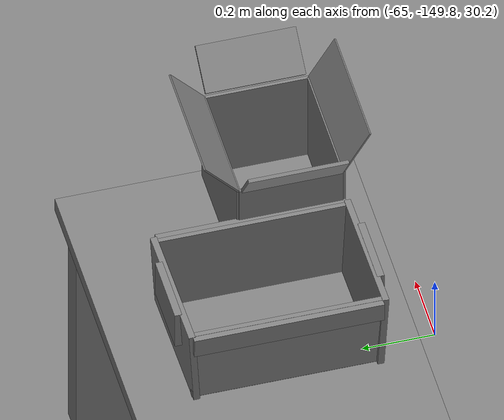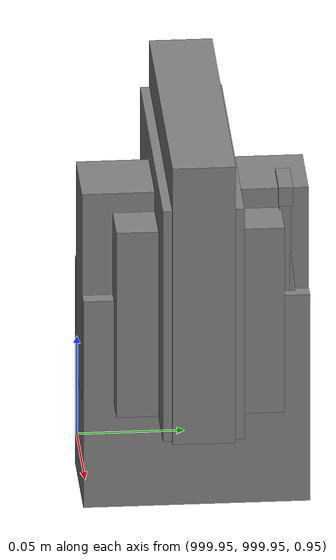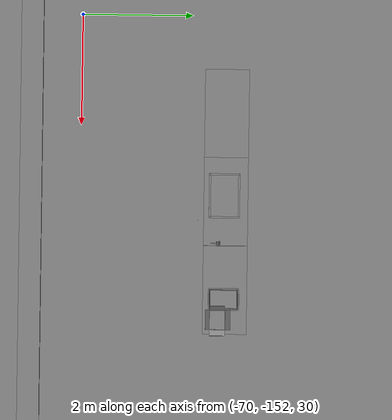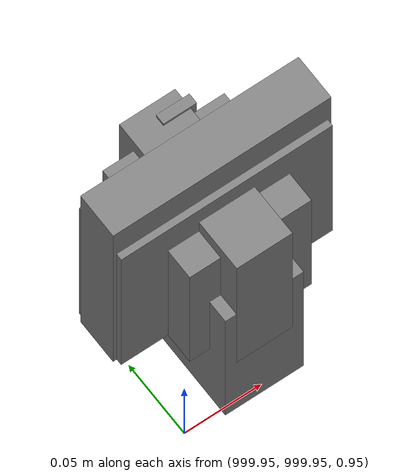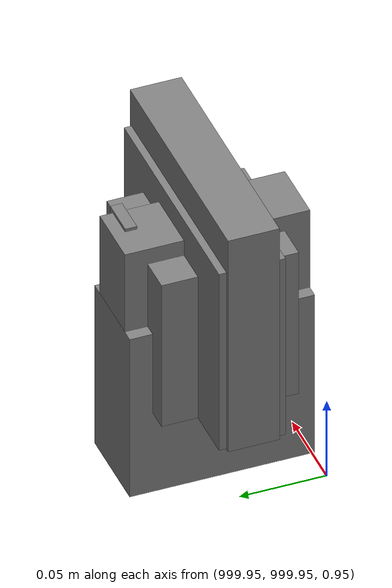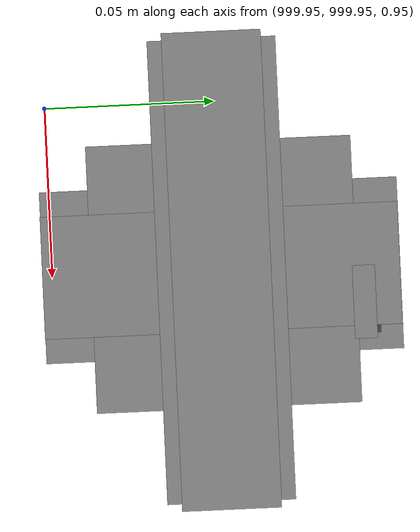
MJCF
<mujoco>
    <option gravity="0.000000000 0.000000000 -9.810000420" timestep="0.0049999999" integrator="implicitfast" density="1.225" viscosity="1.8000001e-05" noslip_iterations="10" iterations="100" sdf_iterations="50">
        <flag multiccd="disable"/>
    </option>
    <size memory="1000M"/>
    <compiler coordinate="local"/>
    <worldbody>
        <light cutoff="30" pos="0 1 1" dir="0 -1 -2"/>
        <light cutoff="30" pos="0 -1 1" dir="0 1 -2"/>
        <body pos="1000.000000000 1000.000000000 1.000000000" euler="0.000011953 0.000005123 -179.999984741" name="openloong_gripper_2f85_fix_base_usda_intel_box">
            <geom contype="1" conaffinity="1" density="1000" type="box" material="" rgba="0.500000000 0.500000000 0.500000000 1.000000000" solimp="0.899999976 0.949999988 0.001000000" friction="1.000000000 0.005000000 0.000100000" solref="0.020000000 1.000000000" margin="0" condim="3" group="0" pos="0.000000000 -0.000067139 0.000082284" quat="0.707106709 0.000000225 0.000000253 0.707106650" size="0.052800003 0.025300000 0.052800003" name="openloong_gripper_2f85_fix_base_usda_geom_0844E2BC_45A3_41CF_AD65_783537871DC2"/>
            <freejoint name="openloong_gripper_2f85_fix_base_usda_intel_box_joint"/>
            <site size="0.005000000 0.005000000 0.005000000" rgba="0.500000000 0.500000000 0.500000000 1.000000000" pos="0.000000000 0.000000000 0.000000000" quat="0.999961913 0.008726500 0.000000000 0.000000000" group="0" type="sphere" name="openloong_gripper_2f85_fix_base_usda_intel_boxsite"/>
        </body>
        <body pos="-65.823242188 -149.772186279 31.168502808" euler="62.248455048 44.663333893 69.260910034" mocap="true" name="spotlight3_SpotLight"/>
        <body pos="1000.000000000 1000.000000000 1.000000000" euler="0.000000000 0.000000000 180.000000000" name="openloong_gripper_2f85_fix_base_usda_wifi_box">
            <geom contype="1" conaffinity="1" density="1000" type="box" material="" rgba="0.500000000 0.500000000 0.500000000 1.000000000" solimp="0.899999976 0.949999988 0.001000000" friction="1.000000000 0.005000000 0.000100000" solref="0.020000000 1.000000000" margin="0" condim="3" group="0" pos="0.000000000 0.000000000 0.058978677" quat="0.000000000 0.000000047 0.000000000 1.000000000" size="0.068499997 0.018999999 0.059000000" name="openloong_gripper_2f85_fix_base_usda_geom_94F48474_3C6E_4245_A422_1599C9E40640"/>
            <freejoint name="openloong_gripper_2f85_fix_base_usda_wifi_box_joint"/>
            <site size="0.005000000 0.005000000 0.005000000" rgba="0.500000000 0.500000000 0.500000000 1.000000000" pos="0.000000000 0.000000000 0.000000000" quat="0.999961913 0.008726500 0.000000000 0.000000000" group="0" type="sphere" name="openloong_gripper_2f85_fix_base_usda_wifi_boxsite"/>
        </body>
        <body pos="-66.262702942 -149.298339844 31.163269043" euler="-69.736663818 17.367757797 70.384620667" mocap="true" name="spotlight6_SpotLight"/>
        <body pos="1000.000000000 1000.000000000 1.000000000" euler="0.000000000 0.000000000 180.000000000" name="openloong_gripper_2f85_fix_base_usda_cpu_fan">
            <geom contype="1" conaffinity="1" density="1000" type="box" material="" rgba="0.500000000 0.500000000 0.500000000 1.000000000" solimp="0.899999976 0.949999988 0.001000000" friction="1.000000000 0.005000000 0.000100000" solref="0.020000000 1.000000000" margin="0" condim="3" group="0" pos="0.000000000 0.000000000 0.070034981" quat="0.000000000 0.000000000 0.000000000 1.000000000" size="0.070700005 0.014699999 0.070700005" name="openloong_gripper_2f85_fix_base_usda_geom_2EB35C7B_8760_46BD_B2B4_127FAFDAB129"/>
            <freejoint name="openloong_gripper_2f85_fix_base_usda_cpu_fan_joint"/>
            <site size="0.005000000 0.005000000 0.005000000" rgba="0.500000000 0.500000000 0.500000000 1.000000000" pos="0.000000000 0.000000000 0.000000000" quat="0.999961913 0.008726535 0.000000000 0.000000000" group="0" type="sphere" name="openloong_gripper_2f85_fix_base_usda_cpu_fancsite"/>
        </body>
        <body pos="1000.000000000 999.999938965 1.000000000" euler="0.000000000 0.000000000 180.000000000" name="openloong_gripper_2f85_fix_base_usda_intelcore_i5">
            <geom contype="1" conaffinity="1" density="1000" type="box" material="" rgba="0.500000000 0.500000000 0.500000000 1.000000000" solimp="0.899999976 0.949999988 0.001000000" friction="1.000000000 0.005000000 0.000100000" solref="0.020000000 1.000000000" margin="0" condim="3" group="0" pos="0.000000000 0.000000000 0.051722717" quat="0.707106709 0.000000000 0.000000000 -0.707106769" size="0.052800000 0.018080002 0.052800000" name="openloong_gripper_2f85_fix_base_usda_geom_11563E76_3506_4815_A102_07C44B33C7FB"/>
            <freejoint name="openloong_gripper_2f85_fix_base_usda_intelcore_i5_joint"/>
            <site size="0.005000000 0.005000000 0.005000000" rgba="0.500000000 0.500000000 0.500000000 1.000000000" pos="0.000000000 0.000000000 0.000000000" quat="0.999961913 0.008726534 0.000000000 0.000000000" group="0" type="sphere" name="openloong_gripper_2f85_fix_base_usda_intelcore_i5site"/>
        </body>
        <body pos="1000.000000000 1000.000000000 1.000000000" euler="0.000000000 0.000000000 180.000000000" name="openloong_gripper_2f85_fix_base_usda_battery_01">
            <geom contype="1" conaffinity="1" density="1000" type="box" material="" rgba="0.500000000 0.500000000 0.500000000 1.000000000" solimp="0.899999976 0.949999988 0.001000000" friction="1.000000000 0.005000000 0.000100000" solref="0.020000000 1.000000000" margin="0" condim="3" group="0" pos="-0.011123657 -0.041940309 0.101691343" quat="1.000000000 0.000000000 0.000000000 0.000000000" size="0.010800000 0.003375000 0.004725000" name="openloong_gripper_2f85_fix_base_usda_geom_014CC3F0_4774_41D6_858E_2460AC3866CA"/>
            <geom contype="1" conaffinity="1" density="1000" type="box" material="" rgba="0.500000000 0.500000000 0.500000000 1.000000000" solimp="0.899999976 0.949999988 0.001000000" friction="1.000000000 0.005000000 0.000100000" solref="0.020000000 1.000000000" margin="0" condim="3" group="0" pos="-0.010876465 -0.044247437 0.047066893" quat="0.998702705 -0.050920475 0.000000000 0.000000000" size="0.009450001 0.002700000 0.024975000" name="openloong_gripper_2f85_fix_base_usda_geom_33C7EB47_FF8B_4ABB_A610_F303A7FF46B3"/>
            <geom contype="1" conaffinity="1" density="1000" type="box" material="" rgba="0.500000000 0.500000000 0.500000000 1.000000000" solimp="0.899999976 0.949999988 0.001000000" friction="1.000000000 0.005000000 0.000100000" solref="0.020000000 1.000000000" margin="0" condim="3" group="0" pos="-0.001235962 -0.000659180 0.047381196" quat="1.000000000 0.000000000 0.000000000 0.000000000" size="0.039420001 0.039150000 0.047250003" name="openloong_gripper_2f85_fix_base_usda_geom_84BCB1FE_1AA8_4B74_AACE_43C0510B90E6"/>
            <geom contype="1" conaffinity="1" density="1000" type="box" material="" rgba="0.500000000 0.500000000 0.500000000 1.000000000" solimp="0.899999976 0.949999988 0.001000000" friction="1.000000000 0.005000000 0.000100000" solref="0.020000000 1.000000000" margin="0" condim="3" group="0" pos="-0.010876465 -0.039138794 0.009851727" quat="1.000000000 0.000000000 0.000000000 0.000000000" size="0.009450001 0.010800000 0.013500000" name="openloong_gripper_2f85_fix_base_usda_geom_6B563C89_3184_4B96_8268_B39283E33CB8"/>
            <geom contype="1" conaffinity="1" density="1000" type="box" material="" rgba="0.500000000 0.500000000 0.500000000 1.000000000" solimp="0.899999976 0.949999988 0.001000000" friction="1.000000000 0.005000000 0.000100000" solref="0.020000000 1.000000000" margin="0" condim="3" group="0" pos="-0.010876465 -0.041528322 0.071508206" quat="1.000000000 0.000000000 0.000000000 0.000000000" size="0.009450001 0.002700000 0.027000001" name="openloong_gripper_2f85_fix_base_usda_geom_7D91298F_4BDF_43B2_8C3B_93327444F1E7"/>
            <freejoint name="openloong_gripper_2f85_fix_base_usda_battery_01_joint"/>
            <site size="0.005000000 0.005000000 0.005000000" rgba="0.500000000 0.500000000 0.500000000 1.000000000" pos="0.000000000 0.000000000 0.000000000" quat="0.999961913 0.008726500 0.000000000 0.000000000" group="0" type="sphere" name="openloong_gripper_2f85_fix_base_usda_battery_01site"/>
        </body>
        <body pos="-65.963981628 -149.026229858 31.170959473" euler="-29.358415604 19.477289200 -163.429824829" mocap="true" name="spotlight4_SpotLight"/>
        <body pos="-64.866622925 -149.383972168 30.183746338" euler="89.999984741 89.999946594 0.000000000" name="openloong_gripper_2f85_fix_base_usda_bluebox_01">
            <geom contype="1" conaffinity="1" density="1000" type="box" material="" rgba="0.500000000 0.500000000 0.500000000 1.000000000" solimp="0.899999976 0.949999988 0.001000000" friction="1.000000000 0.005000000 0.000100000" solref="0.020000000 1.000000000" margin="0" condim="3" group="0" pos="0.276580811 0.187225342 0.000068665" quat="0.707106948 0.000077471 0.707106352 0.000077486" size="0.100000001 0.057999998 0.010000000" name="openloong_gripper_2f85_fix_base_usda_geom_F4600AE8_38E6_406F_9E2B_731CE06BEFC1"/>
            <geom contype="1" conaffinity="1" density="1000" type="box" material="" rgba="0.500000000 0.500000000 0.500000000 1.000000000" solimp="0.899999976 0.949999988 0.001000000" friction="1.000000000 0.005000000 0.000100000" solref="0.020000000 1.000000000" margin="0" condim="3" group="0" pos="0.000000000 0.002883911 0.000000000" quat="0.999999881 0.000000000 0.000000000 0.000000000" size="0.254000008 0.003000000 0.172000006" name="openloong_gripper_2f85_fix_base_usda_geom_35B63776_4A37_4FEA_8862_32B93528EC5E"/>
            <geom contype="1" conaffinity="1" density="1000" type="box" material="" rgba="0.500000000 0.500000000 0.500000000 1.000000000" solimp="0.899999976 0.949999988 0.001000000" friction="1.000000000 0.005000000 0.000100000" solref="0.020000000 1.000000000" margin="0" condim="3" group="0" pos="0.000000000 0.124874115 0.173484802" quat="0.999796331 0.020176515 -0.000000015 0.000000030" size="0.259999990 0.119999997 0.007000000" name="openloong_gripper_2f85_fix_base_usda_geom_DCBEB755_1910_49F8_8013_233FBDD2160B"/>
            <geom contype="1" conaffinity="1" density="1000" type="box" material="" rgba="0.500000000 0.500000000 0.500000000 1.000000000" solimp="0.899999976 0.949999988 0.001000000" friction="1.000000000 0.005000000 0.000100000" solref="0.020000000 1.000000000" margin="0" condim="3" group="0" pos="0.000000000 0.124874115 -0.173469543" quat="0.999796331 -0.020176545 -0.000000015 0.000000000" size="0.259999990 0.119999997 0.007000000" name="openloong_gripper_2f85_fix_base_usda_geom_4E39409F_6B51_4D64_826F_0D831A1943C1"/>
            <geom contype="1" conaffinity="1" density="1000" type="box" material="" rgba="0.500000000 0.500000000 0.500000000 1.000000000" solimp="0.899999976 0.949999988 0.001000000" friction="1.000000000 0.005000000 0.000100000" solref="0.020000000 1.000000000" margin="0" condim="3" group="0" pos="0.000000000 0.214008331 0.188980103" quat="0.999912977 0.013176724 0.000000015 0.000000000" size="0.259999990 0.029999999 0.012500000" name="openloong_gripper_2f85_fix_base_usda_geom_FE75DCF6_0934_4C0D_A133_3B8A90DB2340"/>
            <geom contype="1" conaffinity="1" density="1000" type="box" material="" rgba="0.500000000 0.500000000 0.500000000 1.000000000" solimp="0.899999976 0.949999988 0.001000000" friction="1.000000000 0.005000000 0.000100000" solref="0.020000000 1.000000000" margin="0" condim="3" group="0" pos="-0.258361816 0.125289917 0.001876831" quat="0.702796936 -0.020792112 0.710783124 0.020769298" size="0.189999998 0.119999997 0.009000000" name="openloong_gripper_2f85_fix_base_usda_geom_015AFD1E_13BD_4C02_838E_AE138D1F161D"/>
            <geom contype="1" conaffinity="1" density="1000" type="box" material="" rgba="0.500000000 0.500000000 0.500000000 1.000000000" solimp="0.899999976 0.949999988 0.001000000" friction="1.000000000 0.005000000 0.000100000" solref="0.020000000 1.000000000" margin="0" condim="3" group="0" pos="0.000000000 0.214008331 -0.188980103" quat="0.999912977 -0.013176769 0.000000030 0.000000015" size="0.259999990 0.029999999 0.012500000" name="openloong_gripper_2f85_fix_base_usda_geom_56DF62D5_8878_488F_9A54_0B3DA1CD2ED6"/>
            <geom contype="1" conaffinity="1" density="1000" type="box" material="" rgba="0.500000000 0.500000000 0.500000000 1.000000000" solimp="0.899999976 0.949999988 0.001000000" friction="1.000000000 0.005000000 0.000100000" solref="0.020000000 1.000000000" margin="0" condim="3" group="0" pos="-0.276611328 0.187225342 0.000068665" quat="0.707106650 0.000077441 0.707106709 0.000077456" size="0.100000001 0.057999998 0.010000000" name="openloong_gripper_2f85_fix_base_usda_geom_2C77B603_6C98_4543_B609_CEAA1811EEE9"/>
            <geom contype="1" conaffinity="1" density="1000" type="box" material="" rgba="0.500000000 0.500000000 0.500000000 1.000000000" solimp="0.899999976 0.949999988 0.001000000" friction="1.000000000 0.005000000 0.000100000" solref="0.020000000 1.000000000" margin="0" condim="3" group="0" pos="0.258331299 0.125289917 0.001876831" quat="0.702851415 0.018856421 0.710823774 -0.019329369" size="0.189999998 0.119999997 0.009000000" name="openloong_gripper_2f85_fix_base_usda_geom_9E4D2D69_8C02_4C83_9B27_4CC36F63496D"/>
            <freejoint name="openloong_gripper_2f85_fix_base_usda_bluebox_01_joint"/>
            <site size="0.005000000 0.005000000 0.005000000" rgba="0.500000000 0.500000000 0.500000000 1.000000000" pos="0.000000000 0.000000000 0.000000000" quat="0.999961913 0.008726534 0.000000000 0.000000000" group="0" type="sphere" name="openloong_gripper_2f85_fix_base_usda_bluebox_01site"/>
        </body>
        <body pos="-64.496299744 -149.491867065 30.235729218" euler="0.000000000 0.000000000 89.999946594" name="openloong_gripper_2f85_fix_base_usda_cardboardbox_01">
            <geom contype="1" conaffinity="1" density="1000" type="box" material="" rgba="0.500000000 0.500000000 0.500000000 1.000000000" solimp="0.899999976 0.949999988 0.001000000" friction="1.000000000 0.005000000 0.000100000" solref="0.020000000 1.000000000" margin="0" condim="3" group="0" pos="-0.003166199 -0.004086494 0.005052090" quat="1.000000000 0.000000000 0.000000000 0.000000000" size="0.142499998 0.177500010 0.005000000" name="openloong_gripper_2f85_fix_base_usda_geom_8FFF33A7_6722_4CAD_B2A1_222FC72A35A1"/>
            <geom contype="1" conaffinity="1" density="1000" type="box" material="" rgba="0.500000000 0.500000000 0.500000000 1.000000000" solimp="0.899999976 0.949999988 0.001000000" friction="1.000000000 0.005000000 0.000100000" solref="0.020000000 1.000000000" margin="0" condim="3" group="0" pos="-0.003166199 0.170316696 0.150570869" quat="1.000000000 0.000000000 0.000000000 0.000000000" size="0.142499998 0.005000000 0.149999991" name="openloong_gripper_2f85_fix_base_usda_geom_E815A7D8_D792_4941_B48C_18D509260726"/>
            <geom contype="1" conaffinity="1" density="1000" type="box" material="" rgba="0.500000000 0.500000000 0.500000000 1.000000000" solimp="0.899999976 0.949999988 0.001000000" friction="1.000000000 0.005000000 0.000100000" solref="0.020000000 1.000000000" margin="0" condim="3" group="0" pos="-0.147399902 -0.005307198 0.150570869" quat="1.000000000 0.000000000 0.000000000 0.000000000" size="0.005000000 0.177500010 0.149999991" name="openloong_gripper_2f85_fix_base_usda_geom_CD50D948_8E44_4B55_8E69_3EA326ED351E"/>
            <geom contype="1" conaffinity="1" density="1000" type="box" material="" rgba="0.500000000 0.500000000 0.500000000 1.000000000" solimp="0.899999976 0.949999988 0.001000000" friction="1.000000000 0.005000000 0.000100000" solref="0.020000000 1.000000000" margin="0" condim="3" group="0" pos="0.140275955 -0.005307198 0.150570869" quat="1.000000000 0.000000000 0.000000000 0.000000000" size="0.005000000 0.177500010 0.149999991" name="openloong_gripper_2f85_fix_base_usda_geom_04EAB781_D1D6_4297_AA6E_B89C11EE6BB1"/>
            <geom contype="1" conaffinity="1" density="1000" type="box" material="" rgba="0.500000000 0.500000000 0.500000000 1.000000000" solimp="0.899999976 0.949999988 0.001000000" friction="1.000000000 0.005000000 0.000100000" solref="0.020000000 1.000000000" margin="0" condim="3" group="0" pos="-0.003166199 -0.181550980 0.150570869" quat="1.000000000 0.000000000 0.000000000 0.000000000" size="0.142499998 0.005000000 0.149999991" name="openloong_gripper_2f85_fix_base_usda_geom_C69D450D_4175_4353_A06A_439FD36B3BB1"/>
            <freejoint name="openloong_gripper_2f85_fix_base_usda_cardboardbox_01_joint"/>
            <site size="0.005000000 0.005000000 0.005000000" rgba="0.500000000 0.500000000 0.500000000 1.000000000" pos="0.000000000 0.000000000 0.000000000" quat="0.999961913 0.008726535 0.000000000 0.000000000" group="0" type="sphere" name="openloong_gripper_2f85_fix_base_usda_site_0D7C3DCC_61AF_4CCF_8885_9FC52C236368"/>
            <body pos="0.139160156 -0.004048347 0.301930904" euler="-179.999954224 49.383502960 179.999954224" name="openloong_gripper_2f85_fix_base_usda_A1_006">
                <geom contype="1" conaffinity="1" density="1000" type="box" material="" rgba="0.500000000 0.500000000 0.500000000 1.000000000" solimp="0.899999976 0.949999988 0.001000000" friction="1.000000000 0.005000000 0.000100000" solref="0.020000000 1.000000000" margin="0" condim="3" group="0" pos="-0.071587563 0.000009537 0.001745224" quat="0.999999881 0.000000000 0.000000000 0.000000000" size="0.071249999 0.179999992 0.002500000" name="openloong_gripper_2f85_fix_base_usda_geom_39AE6D57_675A_4006_A9E5_BDFCC26CF9C7"/>
                <joint armature="0" stiffness="0.07" damping="0.0099999998" axis="0.000000 1.000000 0.000000" type="hinge" name="openloong_gripper_2f85_fix_base_usda_A1_006"/>
            </body>
            <body pos="-0.145902634 -0.004086494 0.301938057" euler="-180.000000000 -60.000011444 -180.000000000" name="openloong_gripper_2f85_fix_base_usda_A2_006">
                <geom contype="1" conaffinity="1" density="1000" type="box" material="" rgba="0.500000000 0.500000000 0.500000000 1.000000000" solimp="0.899999976 0.949999988 0.001000000" friction="1.000000000 0.005000000 0.000100000" solref="0.020000000 1.000000000" margin="0" condim="3" group="0" pos="0.071268082 0.000009537 0.002717972" quat="0.000002921 0.000000000 -0.000000030 0.999999881" size="0.071249999 0.179999992 0.002500000" name="openloong_gripper_2f85_fix_base_usda_geom_099A7921_E9B0_4D79_9C6C_FEBE7CC6E77B"/>
                <joint armature="0" stiffness="0.07" damping="0.0099999998" axis="0.000000 1.000000 0.000000" type="hinge" name="openloong_gripper_2f85_fix_base_usda_A2_006"/>
            </body>
            <body pos="-0.003385544 0.175991058 0.301930904" euler="-125.858116150 -0.000004561 0.000002331" name="openloong_gripper_2f85_fix_base_usda_B2_006">
                <geom contype="1" conaffinity="1" density="1000" type="box" material="" rgba="0.500000000 0.500000000 0.500000000 1.000000000" solimp="0.899999976 0.949999988 0.001000000" friction="1.000000000 0.005000000 0.000100000" solref="0.020000000 1.000000000" margin="0" condim="3" group="0" pos="0.000009537 -0.070939064 -0.002470016" quat="0.999614120 0.027776197 -0.000000015 0.000000030" size="0.137500003 0.064999998 0.005000000" name="openloong_gripper_2f85_fix_base_usda_geom_E3880B78_8487_4B2B_9AEA_BFD877BF50EA"/>
                <joint armature="0" stiffness="0.07" damping="0.0099999998" axis="1.000000 0.000000 0.000000" type="hinge" name="openloong_gripper_2f85_fix_base_usda_B2_006"/>
            </body>
            <body pos="-0.003385544 -0.184140205 0.301938057" euler="147.805557251 0.000000000 0.000000000" name="openloong_gripper_2f85_fix_base_usda_B1_006">
                <geom contype="1" conaffinity="1" density="1000" type="box" material="" rgba="0.500000000 0.500000000 0.500000000 1.000000000" solimp="0.899999976 0.949999988 0.001000000" friction="1.000000000 0.005000000 0.000100000" solref="0.020000000 1.000000000" margin="0" condim="3" group="0" pos="-0.000028610 0.070202351 -0.002703667" quat="0.999614179 -0.027776167 0.000000000 0.000000000" size="0.137500003 0.064999998 0.005000000" name="openloong_gripper_2f85_fix_base_usda_geom_3C191CB8_3C71_4F6F_BF3F_E789FF817CDB"/>
                <joint armature="0" stiffness="0.07" damping="0.0099999998" axis="1.000000 0.000000 0.000000" type="hinge" name="openloong_gripper_2f85_fix_base_usda_B1_006"/>
            </body>
        </body>
        <body pos="-65.882858276 -149.481979370 30.229999542" euler="-64.487716675 0.000000000 0.000000000" name="openloong_gripper_2f85_fix_base_usda_Barcode">
            <geom contype="1" conaffinity="1" density="1000" type="box" material="" rgba="0.500000000 0.500000000 0.500000000 1.000000000" solimp="0.899999976 0.949999988 0.001000000" friction="1.000000000 0.005000000 0.000100000" solref="0.020000000 1.000000000" margin="0" condim="3" group="0" pos="0.000000000 0.013038635 0.001419067" quat="0.000000000 0.000000000 0.000000000 1.000000119" size="0.034000002 0.010000000 0.017999999" name="openloong_gripper_2f85_fix_base_usda_geom_3F6027C4_E0AA_4790_A4B9_B4311B3FFD7E"/>
            <geom contype="1" conaffinity="1" density="1000" type="box" material="" rgba="0.500000000 0.500000000 0.500000000 1.000000000" solimp="0.899999976 0.949999988 0.001000000" friction="1.000000000 0.005000000 0.000100000" solref="0.020000000 1.000000000" margin="0" condim="3" group="0" pos="0.000000000 -0.035301208 -0.007095337" quat="0.000000000 0.000000000 -0.043619365 0.999048233" size="0.028999999 0.010000000 0.020000000" name="openloong_gripper_2f85_fix_base_usda_geom_B33C5213_9825_42DE_B6BF_D1FDD2E3598D"/>
            <geom contype="1" conaffinity="1" density="1000" type="box" material="" rgba="0.500000000 0.500000000 0.500000000 1.000000000" solimp="0.899999976 0.949999988 0.001000000" friction="1.000000000 0.005000000 0.000100000" solref="0.020000000 1.000000000" margin="0" condim="3" group="0" pos="0.000000000 -0.043411255 -0.011749268" quat="0.922262907 0.386563420 0.000000000 0.000000000" size="0.026000001 0.010000000 0.020000000" name="openloong_gripper_2f85_fix_base_usda_geom_9633B80E_29BC_4E1A_81AB_A8945EFDE355"/>
            <geom contype="1" conaffinity="1" density="1000" type="box" material="" rgba="0.500000000 0.500000000 0.500000000 1.000000000" solimp="0.899999976 0.949999988 0.001000000" friction="1.000000000 0.005000000 0.000100000" solref="0.020000000 1.000000000" margin="0" condim="3" group="0" pos="0.000000000 -0.016967773 -0.031860352" quat="0.000000000 0.000000000 0.000000000 1.000000119" size="0.008000000 0.010000000 0.013000000" name="openloong_gripper_2f85_fix_base_usda_geom_2B92B0E9_F35B_4B4B_8881_5729AB6C5DE9"/>
            <geom contype="1" conaffinity="1" density="1000" type="box" material="" rgba="0.500000000 0.500000000 0.500000000 1.000000000" solimp="0.899999976 0.949999988 0.001000000" friction="1.000000000 0.005000000 0.000100000" solref="0.020000000 1.000000000" margin="0" condim="3" group="0" pos="0.000000000 -0.001869202 0.000312805" quat="0.953716993 0.300705761 0.000000000 0.000000000" size="0.032000002 0.010000000 0.018999999" name="openloong_gripper_2f85_fix_base_usda_geom_85A6E603_2F78_42B7_8D72_E664396BDB56"/>
            <geom contype="1" conaffinity="1" density="1000" type="box" material="" rgba="0.500000000 0.500000000 0.500000000 1.000000000" solimp="0.899999976 0.949999988 0.001000000" friction="1.000000000 0.005000000 0.000100000" solref="0.020000000 1.000000000" margin="0" condim="3" group="0" pos="0.000000000 -0.019531250 -0.003173828" quat="0.953716993 0.300705761 0.000000000 0.000000000" size="0.030999999 0.010000000 0.020000000" name="openloong_gripper_2f85_fix_base_usda_geom_B701B43B_1EFB_4A8D_A688_DD69581E2DA2"/>
            <geom contype="1" conaffinity="1" density="1000" type="box" material="" rgba="0.500000000 0.500000000 0.500000000 1.000000000" solimp="0.899999976 0.949999988 0.001000000" friction="1.000000000 0.005000000 0.000100000" solref="0.020000000 1.000000000" margin="0" condim="3" group="0" pos="0.000000000 -0.035301208 -0.007095337" quat="0.953716993 0.300705761 0.000000000 0.000000000" size="0.028999999 0.010000000 0.020000000" name="openloong_gripper_2f85_fix_base_usda_geom_5A90C984_1992_430D_A967_6C2712714A7D"/>
            <geom contype="1" conaffinity="1" density="1000" type="box" material="" rgba="0.500000000 0.500000000 0.500000000 1.000000000" solimp="0.899999976 0.949999988 0.001000000" friction="1.000000000 0.005000000 0.000100000" solref="0.020000000 1.000000000" margin="0" condim="3" group="0" pos="0.000000000 -0.042617798 -0.071121216" quat="0.000000000 0.000000000 0.000000000 1.000000119" size="0.013000000 0.021000000 0.059999999" name="openloong_gripper_2f85_fix_base_usda_geom_16C713CE_DDBE_472B_8118_9168EDBC8469"/>
            <freejoint name="openloong_gripper_2f85_fix_base_usda_Barcode_joint"/>
            <site size="0.005000000 0.005000000 0.005000000" rgba="0.500000000 0.500000000 0.500000000 1.000000000" pos="0.000000000 0.000000000 0.000000000" quat="1.000000000 0.000000000 0.000000000 0.000000000" group="0" type="sphere" name="openloong_gripper_2f85_fix_base_usda_Barcode_site"/>
        </body>
        <body pos="-66.745018005 -149.392349243 30.184000015" euler="0.000000000 0.000000000 89.999946594" name="[22333336436851]_Basket_01">
            <geom contype="1" conaffinity="1" density="1000" type="box" material="" rgba="0.500000000 0.500000000 0.500000000 1.000000000" solimp="0.899999976 0.949999988 0.001000000" friction="1.000000000 0.005000000 0.000100000" solref="0.020000000 1.000000000" margin="0" condim="3" group="0" pos="-0.052425385 0.389207840 0.089787483" quat="0.707107008 0.000000000 0.000000000 0.707106411" size="0.014249999 0.014249999 0.059999999" name="[22333336436851]_geom_AE7E7603_82AF_45E7_99A7_37C7405AA5B3"/>
            <geom contype="1" conaffinity="1" density="1000" type="box" material="" rgba="0.500000000 0.500000000 0.500000000 1.000000000" solimp="0.899999976 0.949999988 0.001000000" friction="1.000000000 0.005000000 0.000100000" solref="0.020000000 1.000000000" margin="0" condim="3" group="0" pos="0.264015198 -0.133043289 0.089787483" quat="0.707107008 0.000000000 0.000000000 0.707106411" size="0.014249999 0.014249999 0.059999999" name="[22333336436851]_geom_A0B48F9B_A87F_4835_BEB4_3F26FCB7E4C2"/>
            <geom contype="1" conaffinity="1" density="1000" type="box" material="" rgba="0.500000000 0.500000000 0.500000000 1.000000000" solimp="0.899999976 0.949999988 0.001000000" friction="1.000000000 0.005000000 0.000100000" solref="0.020000000 1.000000000" margin="0" condim="3" group="0" pos="-0.264015198 -0.265548706 0.089793205" quat="0.707107008 0.000000000 0.000000000 0.707106411" size="0.014249999 0.014249999 0.059999999" name="[22333336436851]_geom_25575189_E1C0_40A4_844F_9A1AE6943C64"/>
            <geom contype="1" conaffinity="1" density="1000" type="box" material="" rgba="0.500000000 0.500000000 0.500000000 1.000000000" solimp="0.899999976 0.949999988 0.001000000" friction="1.000000000 0.005000000 0.000100000" solref="0.020000000 1.000000000" margin="0" condim="3" group="0" pos="-0.160263062 -0.389322281 0.089793205" quat="0.707107008 0.000000000 0.000000000 0.707106411" size="0.014249999 0.014249999 0.059999999" name="[22333336436851]_geom_A060DAD1_A7B6_4AF4_9ECF_7FC10A8F5A06"/>
            <geom contype="1" conaffinity="1" density="1000" type="box" material="" rgba="0.500000000 0.500000000 0.500000000 1.000000000" solimp="0.899999976 0.949999988 0.001000000" friction="1.000000000 0.005000000 0.000100000" solref="0.020000000 1.000000000" margin="0" condim="3" group="0" pos="0.162265778 -0.389322281 0.089787483" quat="0.707107008 0.000000000 0.000000000 0.707106411" size="0.014249999 0.014249999 0.059999999" name="[22333336436851]_geom_2185A04A_6F32_4888_A421_D13AB3235A6F"/>
            <geom contype="1" conaffinity="1" density="1000" type="box" material="" rgba="0.500000000 0.500000000 0.500000000 1.000000000" solimp="0.899999976 0.949999988 0.001000000" friction="1.000000000 0.005000000 0.000100000" solref="0.020000000 1.000000000" margin="0" condim="3" group="0" pos="0.264015198 0.389207840 0.089787483" quat="0.707107008 0.000000000 0.000000000 0.707106411" size="0.014249999 0.014249999 0.059999999" name="[22333336436851]_geom_49A02F93_9867_44F4_890F_65246578ACDA"/>
            <geom contype="1" conaffinity="1" density="1000" type="box" material="" rgba="0.500000000 0.500000000 0.500000000 1.000000000" solimp="0.899999976 0.949999988 0.001000000" friction="1.000000000 0.005000000 0.000100000" solref="0.020000000 1.000000000" margin="0" condim="3" group="0" pos="-0.264015198 -0.133043289 0.089793205" quat="0.707107008 0.000000000 0.000000000 0.707106411" size="0.014249999 0.014249999 0.059999999" name="[22333336436851]_geom_72F84020_D3FC_4B8D_BC8B_7CAB937C0CB2"/>
            <geom contype="1" conaffinity="1" density="1000" type="box" material="" rgba="0.500000000 0.500000000 0.500000000 1.000000000" solimp="0.899999976 0.949999988 0.001000000" friction="1.000000000 0.005000000 0.000100000" solref="0.020000000 1.000000000" margin="0" condim="3" group="0" pos="-0.264026642 0.269256592 0.089793205" quat="0.707107008 0.000000000 0.000000000 0.707106411" size="0.014249999 0.014249999 0.059999999" name="[22333336436851]_geom_E3D1585C_4F11_4727_A2C8_94389A10E4FC"/>
            <geom contype="1" conaffinity="1" density="1000" type="box" material="" rgba="0.500000000 0.500000000 0.500000000 1.000000000" solimp="0.899999976 0.949999988 0.001000000" friction="1.000000000 0.005000000 0.000100000" solref="0.020000000 1.000000000" margin="0" condim="3" group="0" pos="0.054462433 0.389207840 0.089787483" quat="0.707107008 0.000000000 0.000000000 0.707106411" size="0.014249999 0.014249999 0.059999999" name="[22333336436851]_geom_7DC9EAE7_B988_4372_B928_69D092FE0B79"/>
            <geom contype="1" conaffinity="1" density="1000" type="box" material="" rgba="0.500000000 0.500000000 0.500000000 1.000000000" solimp="0.899999976 0.949999988 0.001000000" friction="1.000000000 0.005000000 0.000100000" solref="0.020000000 1.000000000" margin="0" condim="3" group="0" pos="0.054462433 -0.389322281 0.089787483" quat="0.707107008 0.000000000 0.000000000 0.707106411" size="0.014249999 0.014249999 0.059999999" name="[22333336436851]_geom_FDB4822F_1F5E_462C_B920_639223CE3C64"/>
            <geom contype="1" conaffinity="1" density="1000" type="box" material="" rgba="0.500000000 0.500000000 0.500000000 1.000000000" solimp="0.899999976 0.949999988 0.001000000" friction="1.000000000 0.005000000 0.000100000" solref="0.020000000 1.000000000" margin="0" condim="3" group="0" pos="0.264015198 0.269256592 0.089793205" quat="0.707107008 0.000000000 0.000000000 0.707106411" size="0.014249999 0.014249999 0.059999999" name="[22333336436851]_geom_E857EE10_EF9A_43C8_A88D_B2CB596DFD48"/>
            <geom contype="1" conaffinity="1" density="1000" type="box" material="" rgba="0.500000000 0.500000000 0.500000000 1.000000000" solimp="0.899999976 0.949999988 0.001000000" friction="1.000000000 0.005000000 0.000100000" solref="0.020000000 1.000000000" margin="0" condim="3" group="0" pos="0.264015198 -0.389322281 0.089787483" quat="0.707107008 0.000000000 0.000000000 0.707106411" size="0.014249999 0.014249999 0.059999999" name="[22333336436851]_geom_C0844C17_4ABA_4215_964B_3174FE89337E"/>
            <geom contype="1" conaffinity="1" density="1000" type="box" material="" rgba="0.500000000 0.500000000 0.500000000 1.000000000" solimp="0.899999976 0.949999988 0.001000000" friction="1.000000000 0.005000000 0.000100000" solref="0.020000000 1.000000000" margin="0" condim="3" group="0" pos="0.000000000 0.000000000 0.015998840" quat="0.707107008 0.000000000 0.000000000 0.707106411" size="0.403499991 0.279000014 0.015750000" name="[22333336436851]_geom_498B56B0_ADD0_42B0_9EE3_BB27C54EADC4"/>
            <geom contype="1" conaffinity="1" density="1000" type="box" material="" rgba="0.500000000 0.500000000 0.500000000 1.000000000" solimp="0.899999976 0.949999988 0.001000000" friction="1.000000000 0.005000000 0.000100000" solref="0.020000000 1.000000000" margin="0" condim="3" group="0" pos="0.000000000 -0.389476776 0.163619041" quat="0.707107008 0.000000000 0.000000000 0.707106411" size="0.015000000 0.277500004 0.015750000" name="[22333336436851]_geom_EF4AB688_98D5_4031_9CEA_5BA3185EDA56"/>
            <geom contype="1" conaffinity="1" density="1000" type="box" material="" rgba="0.500000000 0.500000000 0.500000000 1.000000000" solimp="0.899999976 0.949999988 0.001000000" friction="1.000000000 0.005000000 0.000100000" solref="0.020000000 1.000000000" margin="0" condim="3" group="0" pos="0.162265778 0.389207840 0.089787483" quat="0.707107008 0.000000000 0.000000000 0.707106411" size="0.014249999 0.014249999 0.059999999" name="[22333336436851]_geom_3E6D83BD_06F5_4890_B0A5_B13415667E68"/>
            <geom contype="1" conaffinity="1" density="1000" type="box" material="" rgba="0.500000000 0.500000000 0.500000000 1.000000000" solimp="0.899999976 0.949999988 0.001000000" friction="1.000000000 0.005000000 0.000100000" solref="0.020000000 1.000000000" margin="0" condim="3" group="0" pos="0.000000000 0.389471054 0.163619041" quat="0.707107008 0.000000000 0.000000000 0.707106411" size="0.015000000 0.277500004 0.015750000" name="[22333336436851]_geom_04FFBA56_A8B5_46AD_B7FA_A757E66DD9D8"/>
            <geom contype="1" conaffinity="1" density="1000" type="box" material="" rgba="0.500000000 0.500000000 0.500000000 1.000000000" solimp="0.899999976 0.949999988 0.001000000" friction="1.000000000 0.005000000 0.000100000" solref="0.020000000 1.000000000" margin="0" condim="3" group="0" pos="-0.263511658 0.000000000 0.163619041" quat="0.707107008 0.000000000 0.000000000 0.707106411" size="0.403499991 0.015000000 0.015750000" name="[22333336436851]_geom_AFEAA0A3_70E8_4EDB_930E_3B06AADBDAE9"/>
            <geom contype="1" conaffinity="1" density="1000" type="box" material="" rgba="0.500000000 0.500000000 0.500000000 1.000000000" solimp="0.899999976 0.949999988 0.001000000" friction="1.000000000 0.005000000 0.000100000" solref="0.020000000 1.000000000" margin="0" condim="3" group="0" pos="-0.264015198 0.141334534 0.089793205" quat="0.707107008 0.000000000 0.000000000 0.707106411" size="0.014249999 0.014249999 0.059999999" name="[22333336436851]_geom_58B6061D_AE43_470C_BCFD_34A6E62EC752"/>
            <geom contype="1" conaffinity="1" density="1000" type="box" material="" rgba="0.500000000 0.500000000 0.500000000 1.000000000" solimp="0.899999976 0.949999988 0.001000000" friction="1.000000000 0.005000000 0.000100000" solref="0.020000000 1.000000000" margin="0" condim="3" group="0" pos="0.264015198 -0.265548706 0.089787483" quat="0.707107008 0.000000000 0.000000000 0.707106411" size="0.014249999 0.014249999 0.059999999" name="[22333336436851]_geom_C8DAA7CD_D463_46F9_A708_F6B292D50860"/>
            <geom contype="1" conaffinity="1" density="1000" type="box" material="" rgba="0.500000000 0.500000000 0.500000000 1.000000000" solimp="0.899999976 0.949999988 0.001000000" friction="1.000000000 0.005000000 0.000100000" solref="0.020000000 1.000000000" margin="0" condim="3" group="0" pos="-0.160263062 0.389207840 0.089787483" quat="0.707107008 0.000000000 0.000000000 0.707106411" size="0.014249999 0.014249999 0.059999999" name="[22333336436851]_geom_0348484A_3782_4C0B_901D_A1A6125FB476"/>
            <geom contype="1" conaffinity="1" density="1000" type="box" material="" rgba="0.500000000 0.500000000 0.500000000 1.000000000" solimp="0.899999976 0.949999988 0.001000000" friction="1.000000000 0.005000000 0.000100000" solref="0.020000000 1.000000000" margin="0" condim="3" group="0" pos="-0.052425385 -0.389322281 0.089787483" quat="0.707107008 0.000000000 0.000000000 0.707106411" size="0.014249999 0.014249999 0.059999999" name="[22333336436851]_geom_E50D64B7_50F2_4F46_B22E_232D731BAAB7"/>
            <geom contype="1" conaffinity="1" density="1000" type="box" material="" rgba="0.500000000 0.500000000 0.500000000 1.000000000" solimp="0.899999976 0.949999988 0.001000000" friction="1.000000000 0.005000000 0.000100000" solref="0.020000000 1.000000000" margin="0" condim="3" group="0" pos="-0.264026642 -0.389322281 0.089793205" quat="0.707107008 0.000000000 0.000000000 0.707106411" size="0.014249999 0.014249999 0.059999999" name="[22333336436851]_geom_7AD7EB32_1BE1_4054_897B_A9F0FA43E6A8"/>
            <geom contype="1" conaffinity="1" density="1000" type="box" material="" rgba="0.500000000 0.500000000 0.500000000 1.000000000" solimp="0.899999976 0.949999988 0.001000000" friction="1.000000000 0.005000000 0.000100000" solref="0.020000000 1.000000000" margin="0" condim="3" group="0" pos="0.264015198 0.141334534 0.089787483" quat="0.707107008 0.000000000 0.000000000 0.707106411" size="0.014249999 0.014249999 0.059999999" name="[22333336436851]_geom_F07B66E8_022C_470D_9C2D_C77F69085479"/>
            <geom contype="1" conaffinity="1" density="1000" type="box" material="" rgba="0.500000000 0.500000000 0.500000000 1.000000000" solimp="0.899999976 0.949999988 0.001000000" friction="1.000000000 0.005000000 0.000100000" solref="0.020000000 1.000000000" margin="0" condim="3" group="0" pos="-0.264015198 0.389207840 0.089793205" quat="0.707107008 0.000000000 0.000000000 0.707106411" size="0.014249999 0.014249999 0.059999999" name="[22333336436851]_geom_DB97F345_EEBA_430A_A16D_17DAB8680A81"/>
            <geom contype="1" conaffinity="1" density="1000" type="box" material="" rgba="0.500000000 0.500000000 0.500000000 1.000000000" solimp="0.899999976 0.949999988 0.001000000" friction="1.000000000 0.005000000 0.000100000" solref="0.020000000 1.000000000" margin="0" condim="3" group="0" pos="0.264015198 0.004480362 0.089787483" quat="0.707107008 0.000000000 0.000000000 0.707106411" size="0.014249999 0.014249999 0.059999999" name="[22333336436851]_geom_1F0E3707_2A58_466D_A7CE_ABF80E610867"/>
            <geom contype="1" conaffinity="1" density="1000" type="box" material="" rgba="0.500000000 0.500000000 0.500000000 1.000000000" solimp="0.899999976 0.949999988 0.001000000" friction="1.000000000 0.005000000 0.000100000" solref="0.020000000 1.000000000" margin="0" condim="3" group="0" pos="0.263694763 -0.000011444 0.163619041" quat="0.707107008 0.000000000 0.000000000 0.707106411" size="0.403499991 0.015000000 0.015750000" name="[22333336436851]_geom_1FC61B38_A8B3_466A_9591_EA92F04DA458"/>
            <geom contype="1" conaffinity="1" density="1000" type="box" material="" rgba="0.500000000 0.500000000 0.500000000 1.000000000" solimp="0.899999976 0.949999988 0.001000000" friction="1.000000000 0.005000000 0.000100000" solref="0.020000000 1.000000000" margin="0" condim="3" group="0" pos="-0.264015198 0.004480362 0.089793205" quat="0.707107008 0.000000000 0.000000000 0.707106411" size="0.014249999 0.014249999 0.059999999" name="[22333336436851]_geom_DC1CAE1F_D18E_4EE6_9994_07A7B172B44A"/>
            <freejoint name="[22333336436851]_joint_8D7BBA71_35BF_4342_B429_43B359DC6440"/>
        </body>
        <body pos="0.000000000 0.000000000 0.000000000" euler="0.000000000 0.000000000 0.000000000" name="Static Objects_Static Objects">
            <geom contype="1" conaffinity="1" density="1000" type="box" material="" rgba="0.500000000 0.500000000 0.500000000 1.000000000" solimp="0.899999976 0.949999988 0.001000000" friction="1.000000000 0.005000000 0.000100000" solref="0.020000000 1.000000000" margin="0" condim="3" group="0" pos="-67.544113159 -149.365814209 29.727830887" quat="0.500000417 0.499999970 0.499999553 0.499999970" size="0.381000012 0.319999993 0.041000001" name="Static Objects_geom_41FCA31B_56D1_4F83_8C66_CD7B18CF8F31"/>
            <geom contype="1" conaffinity="1" density="1000" type="box" material="" rgba="0.500000000 0.500000000 0.500000000 1.000000000" solimp="0.899999976 0.949999988 0.001000000" friction="1.000000000 0.005000000 0.000100000" solref="0.020000000 1.000000000" margin="0" condim="3" group="0" pos="-68.239501953 -149.365814209 30.086868286" quat="0.500000417 0.499999970 0.499999553 0.499999970" size="0.370999992 0.039500002 0.745000005" name="Static Objects_geom_D241C079_65C7_4671_85BB_63DE8025A56B"/>
            <geom contype="1" conaffinity="1" density="1000" type="box" material="" rgba="0.500000000 0.500000000 0.500000000 1.000000000" solimp="0.899999976 0.949999988 0.001000000" friction="1.000000000 0.005000000 0.000100000" solref="0.020000000 1.000000000" margin="0" condim="3" group="0" pos="-68.239501953 -149.365814209 30.147235870" quat="0.500000417 0.499999970 0.499999553 0.499999970" size="0.400000006 0.022000000 0.800000012" name="Static Objects_geom_02237CB1_C64C_4D0F_AFFA_2B2728053F7D"/>
            <geom contype="1" conaffinity="1" density="1000" type="box" material="" rgba="0.500000000 0.500000000 0.500000000 1.000000000" solimp="0.899999976 0.949999988 0.001000000" friction="1.000000000 0.005000000 0.000100000" solref="0.020000000 1.000000000" margin="0" condim="3" group="0" pos="-68.934890747 -149.365814209 29.727830887" quat="0.500000417 0.499999970 0.499999553 0.499999970" size="0.381000012 0.319999993 0.041000001" name="Static Objects_geom_BA4A7A0F_F17C_4EA3_8BBB_213607E3494F"/>
            <geom contype="1" conaffinity="1" density="1000" type="box" material="" rgba="0.500000000 0.500000000 0.500000000 1.000000000" solimp="0.899999976 0.949999988 0.001000000" friction="1.000000000 0.005000000 0.000100000" solref="0.020000000 1.000000000" margin="0" condim="3" group="0" pos="-68.239501953 -149.365814209 29.561563492" quat="0.500000417 0.499999970 0.499999553 0.499999970" size="0.020000000 0.022000000 0.660000026" name="Static Objects_geom_99A9D987_431B_4823_A4B3_5B509915D575"/>
            <geom contype="1" conaffinity="1" density="1000" type="box" material="" rgba="0.500000000 0.500000000 0.500000000 1.000000000" solimp="0.899999976 0.949999988 0.001000000" friction="1.000000000 0.005000000 0.000100000" solref="0.020000000 1.000000000" margin="0" condim="3" group="0" pos="-65.945671082 -149.365814209 29.727830887" quat="0.500000417 0.499999970 0.499999553 0.499999970" size="0.381000012 0.319999993 0.041000001" name="Static Objects_geom_FD11E25D_BB2A_4A51_8C77_61EB3E260758"/>
            <geom contype="1" conaffinity="1" density="1000" type="box" material="" rgba="0.500000000 0.500000000 0.500000000 1.000000000" solimp="0.899999976 0.949999988 0.001000000" friction="1.000000000 0.005000000 0.000100000" solref="0.020000000 1.000000000" margin="0" condim="3" group="0" pos="-66.641059875 -149.365814209 30.086868286" quat="0.500000417 0.499999970 0.499999553 0.499999970" size="0.370999992 0.039500002 0.745000005" name="Static Objects_geom_3C1502B5_3618_471A_A523_956118DABCB3"/>
            <geom contype="1" conaffinity="1" density="1000" type="box" material="" rgba="0.500000000 0.500000000 0.500000000 1.000000000" solimp="0.899999976 0.949999988 0.001000000" friction="1.000000000 0.005000000 0.000100000" solref="0.020000000 1.000000000" margin="0" condim="3" group="0" pos="-66.641059875 -149.365814209 30.147235870" quat="0.500000417 0.499999970 0.499999553 0.499999970" size="0.400000006 0.022000000 0.800000012" name="Static Objects_geom_8C140096_6DA7_4C83_8EAD_D712467EAB03"/>
            <geom contype="1" conaffinity="1" density="1000" type="box" material="" rgba="0.500000000 0.500000000 0.500000000 1.000000000" solimp="0.899999976 0.949999988 0.001000000" friction="1.000000000 0.005000000 0.000100000" solref="0.020000000 1.000000000" margin="0" condim="3" group="0" pos="-67.336448669 -149.365814209 29.727830887" quat="0.500000417 0.499999970 0.499999553 0.499999970" size="0.381000012 0.319999993 0.041000001" name="Static Objects_geom_C02EE1CA_D21F_4F14_98D5_0BE7009EF5E3"/>
            <geom contype="1" conaffinity="1" density="1000" type="box" material="" rgba="0.500000000 0.500000000 0.500000000 1.000000000" solimp="0.899999976 0.949999988 0.001000000" friction="1.000000000 0.005000000 0.000100000" solref="0.020000000 1.000000000" margin="0" condim="3" group="0" pos="-66.641059875 -149.365814209 29.561563492" quat="0.500000417 0.499999970 0.499999553 0.499999970" size="0.020000000 0.022000000 0.660000026" name="Static Objects_geom_636D7365_E900_4FFC_8EE9_195B353EA439"/>
            <geom contype="1" conaffinity="1" density="1000" type="box" material="" rgba="0.500000000 0.500000000 0.500000000 1.000000000" solimp="0.899999976 0.949999988 0.001000000" friction="1.000000000 0.005000000 0.000100000" solref="0.020000000 1.000000000" margin="0" condim="3" group="0" pos="-64.338577271 -149.365814209 29.727830887" quat="0.500000417 0.499999970 0.499999553 0.499999970" size="0.381000012 0.319999993 0.041000001" name="Static Objects_geom_257CEC8A_C1CA_4352_862D_9F6743C8E747"/>
            <geom contype="1" conaffinity="1" density="1000" type="box" material="" rgba="0.500000000 0.500000000 0.500000000 1.000000000" solimp="0.899999976 0.949999988 0.001000000" friction="1.000000000 0.005000000 0.000100000" solref="0.020000000 1.000000000" margin="0" condim="3" group="0" pos="-65.033966064 -149.365814209 30.086868286" quat="0.500000417 0.499999970 0.499999553 0.499999970" size="0.370999992 0.039500002 0.745000005" name="Static Objects_geom_2D2ED0EC_81D9_4ADD_994E_495774782FFD"/>
            <geom contype="1" conaffinity="1" density="1000" type="box" material="" rgba="0.500000000 0.500000000 0.500000000 1.000000000" solimp="0.899999976 0.949999988 0.001000000" friction="1.000000000 0.005000000 0.000100000" solref="0.020000000 1.000000000" margin="0" condim="3" group="0" pos="-65.033966064 -149.365814209 30.147235870" quat="0.500000417 0.499999970 0.499999553 0.499999970" size="0.400000006 0.022000000 0.800000012" name="Static Objects_geom_C93EE960_7185_46C8_B71B_0A05A7CEE6D9"/>
            <geom contype="1" conaffinity="1" density="1000" type="box" material="" rgba="0.500000000 0.500000000 0.500000000 1.000000000" solimp="0.899999976 0.949999988 0.001000000" friction="1.000000000 0.005000000 0.000100000" solref="0.020000000 1.000000000" margin="0" condim="3" group="0" pos="-65.729354858 -149.365814209 29.727830887" quat="0.500000417 0.499999970 0.499999553 0.499999970" size="0.381000012 0.319999993 0.041000001" name="Static Objects_geom_BC6781AB_FB6E_43C9_947E_2924688B9BA8"/>
            <geom contype="1" conaffinity="1" density="1000" type="box" material="" rgba="0.500000000 0.500000000 0.500000000 1.000000000" solimp="0.899999976 0.949999988 0.001000000" friction="1.000000000 0.005000000 0.000100000" solref="0.020000000 1.000000000" margin="0" condim="3" group="0" pos="-65.033966064 -149.365814209 29.561563492" quat="0.500000417 0.499999970 0.499999553 0.499999970" size="0.020000000 0.022000000 0.660000026" name="Static Objects_geom_5B283259_C728_4E1A_A39F_1C27FE373244"/>
            <geom contype="1" conaffinity="1" density="1000" type="box" material="" rgba="0.500000000 0.500000000 0.500000000 1.000000000" solimp="0.899999976 0.949999988 0.001000000" friction="1.000000000 0.005000000 0.000100000" solref="0.020000000 1.000000000" margin="0" condim="3" group="0" pos="-61.754566193 -137.853729248 33.906845093" quat="0.707107067 0.000000000 0.000000000 0.707106471" size="0.759999990 0.759999990 4.500000000" name="Static Objects_geom_0CDC99DB_4E44_4377_BDA3_4AA326D062D4"/>
            <geom contype="1" conaffinity="1" density="1000" type="box" material="" rgba="0.500000000 0.500000000 0.500000000 1.000000000" solimp="0.899999976 0.949999988 0.001000000" friction="1.000000000 0.005000000 0.000100000" solref="0.020000000 1.000000000" margin="0" condim="3" group="0" pos="-57.511135101 -144.927108765 31.707921982" quat="1.000000000 0.000000000 0.000000000 0.000000000" size="0.200000003 8.000000000 2.299999952" name="Static Objects_geom_FCE2B0B0_9DC9_483C_990B_2FD2C82639F6"/>
            <geom contype="1" conaffinity="1" density="1000" type="box" material="" rgba="0.500000000 0.500000000 0.500000000 1.000000000" solimp="0.899999976 0.949999988 0.001000000" friction="1.000000000 0.005000000 0.000100000" solref="0.020000000 1.000000000" margin="0" condim="3" group="0" pos="-80.517646790 -157.574050903 31.688196182" quat="0.707107067 0.000000000 0.000000000 0.707106471" size="0.600000024 0.600000024 2.299999952" name="Static Objects_geom_84BBCC95_C4D9_476D_963E_A47C701F6E20"/>
            <geom contype="1" conaffinity="1" density="1000" type="box" material="" rgba="0.500000000 0.500000000 0.500000000 1.000000000" solimp="0.899999976 0.949999988 0.001000000" friction="1.000000000 0.005000000 0.000100000" solref="0.020000000 1.000000000" margin="0" condim="3" group="0" pos="-80.711044312 -147.414932251 31.666158676" quat="1.000000000 0.000000000 0.000000000 0.000000000" size="0.200000003 10.000000000 2.299999952" name="Static Objects_geom_B013DD00_060D_4586_8322_5029ABA25FB4"/>
            <geom contype="1" conaffinity="1" density="1000" type="box" material="" rgba="0.500000000 0.500000000 0.500000000 1.000000000" solimp="0.899999976 0.949999988 0.001000000" friction="1.000000000 0.005000000 0.000100000" solref="0.020000000 1.000000000" margin="0" condim="3" group="0" pos="-57.687217712 -137.434692383 31.688196182" quat="0.707107067 0.000000000 0.000000000 0.707106471" size="0.600000024 0.600000024 2.299999952" name="Static Objects_geom_5BF79D9F_9261_4529_B7B1_1FC34522F130"/>
            <geom contype="1" conaffinity="1" density="1000" type="box" material="" rgba="0.500000000 0.500000000 0.500000000 1.000000000" solimp="0.899999976 0.949999988 0.001000000" friction="1.000000000 0.005000000 0.000100000" solref="0.020000000 1.000000000" margin="0" condim="3" group="0" pos="-69.537033081 -140.263229370 31.714921951" quat="0.707107067 0.000000000 0.000000000 0.707106471" size="0.759999990 4.500000000 2.299999952" name="Static Objects_geom_5BF1A8E6_16D7_4E8C_B141_0C96E9A86A8A"/>
            <geom contype="1" conaffinity="1" density="1000" type="box" material="" rgba="0.500000000 0.500000000 0.500000000 1.000000000" solimp="0.899999976 0.949999988 0.001000000" friction="1.000000000 0.005000000 0.000100000" solref="0.020000000 1.000000000" margin="0" condim="3" group="0" pos="-80.073638916 -137.853713989 33.906845093" quat="0.707107067 0.000000000 0.000000000 0.707106471" size="0.759999990 0.759999990 4.500000000" name="Static Objects_geom_C29D094F_9489_4D2E_BD0E_684C200BBEF0"/>
            <geom contype="1" conaffinity="1" density="1000" type="box" material="" rgba="0.500000000 0.500000000 0.500000000 1.000000000" solimp="0.899999976 0.949999988 0.001000000" friction="1.000000000 0.005000000 0.000100000" solref="0.020000000 1.000000000" margin="0" condim="3" group="0" pos="-73.406707764 -155.734664917 31.707921982" quat="1.000000000 0.000000000 0.000000000 0.000000000" size="0.200000003 3.000000000 2.299999952" name="Static Objects_geom_86DC734E_952B_4765_8F9F_3529B54A1001"/>
            <geom contype="1" conaffinity="1" density="1000" type="box" material="" rgba="0.500000000 0.500000000 0.500000000 1.000000000" solimp="0.899999976 0.949999988 0.001000000" friction="1.000000000 0.005000000 0.000100000" solref="0.020000000 1.000000000" margin="0" condim="3" group="0" pos="-68.497543335 -137.448257446 31.707921982" quat="0.707107067 0.000000000 0.000000000 0.707106471" size="0.200000003 14.000000000 2.299999952" name="Static Objects_geom_82584F09_0EA7_44BB_8BEA_53CD8BB7D8F0"/>
            <geom contype="1" conaffinity="1" density="1000" type="cylinder" material="" rgba="0.500000000 0.500000000 0.500000000 1.000000000" solimp="0.899999976 0.949999988 0.001000000" friction="1.000000000 0.005000000 0.000100000" solref="0.020000000 1.000000000" margin="0" condim="3" group="0" pos="-68.868522644 -142.134506226 31.711090088" quat="0.707107067 0.000000000 0.000000000 0.707106471" size="0.509999990 2.299999952 1.000000000" name="Static Objects_geom_72A9FF66_4683_4714_B0D0_2D10F49C3318"/>
            <geom contype="1" conaffinity="1" density="1000" type="plane" material="" rgba="0.500000000 0.500000000 0.500000000 1.000000000" solimp="0.899999976 0.949999988 0.001000000" friction="1.000000000 0.005000000 0.000100000" solref="0.020000000 1.000000000" margin="0" condim="3" group="0" pos="-72.873703003 -147.131927490 29.409669876" quat="1.000000000 0.000000000 0.000000000 0.000000000" size="18.000000000 14.000000000 1.000000000" name="Static Objects_geom_0D81B19B_E1F0_474C_9950_F3AA4D9EAD85"/>
            <geom contype="1" conaffinity="1" density="1000" type="box" material="" rgba="0.500000000 0.500000000 0.500000000 1.000000000" solimp="0.899999976 0.949999988 0.001000000" friction="1.000000000 0.005000000 0.000100000" solref="0.020000000 1.000000000" margin="0" condim="3" group="0" pos="-79.943580627 -157.782272339 31.707921982" quat="0.707107067 0.000000000 0.000000000 0.707106471" size="0.200000003 7.000000000 2.299999952" name="Static Objects_geom_D680B645_B206_425C_8B54_2CEE5A89EA34"/>
            <geom contype="1" conaffinity="1" density="1000" type="box" material="" rgba="0.500000000 0.500000000 0.500000000 1.000000000" solimp="0.899999976 0.949999988 0.001000000" friction="1.000000000 0.005000000 0.000100000" solref="0.020000000 1.000000000" margin="0" condim="3" group="0" pos="-65.421028137 -152.903442383 31.707921982" quat="0.707107067 0.000000000 0.000000000 0.707106471" size="0.200000003 7.800000191 2.299999952" name="Static Objects_geom_BEF28423_873D_425F_AC9D_AD9437D38658"/>
            <geom contype="1" conaffinity="1" density="1000" type="box" material="" rgba="0.500000000 0.500000000 0.500000000 1.000000000" solimp="0.899999976 0.949999988 0.001000000" friction="1.000000000 0.005000000 0.000100000" solref="0.020000000 1.000000000" margin="0" condim="3" group="0" pos="-74.776908875 -149.964416504 31.688196182" quat="1.000000000 0.000000000 0.000000000 0.000000000" size="0.600000024 0.409999996 2.299999952" name="Static Objects_geom_4851E1C5_C4B5_4E41_9C3C_645C51AD7875"/>
            <geom contype="1" conaffinity="1" density="1000" type="cylinder" material="" rgba="0.500000000 0.500000000 0.500000000 1.000000000" solimp="0.899999976 0.949999988 0.001000000" friction="1.000000000 0.005000000 0.000100000" solref="0.020000000 1.000000000" margin="0" condim="3" group="0" pos="-60.161884308 -142.134506226 31.711090088" quat="0.707107067 0.000000000 0.000000000 0.707106471" size="0.509999990 2.299999952 1.000000000" name="Static Objects_geom_DC843A1E_48E6_47FC_A7CB_003583CE3173"/>
            <geom contype="1" conaffinity="1" density="1000" type="cylinder" material="" rgba="0.500000000 0.500000000 0.500000000 1.000000000" solimp="0.899999976 0.949999988 0.001000000" friction="1.000000000 0.005000000 0.000100000" solref="0.020000000 1.000000000" margin="0" condim="3" group="0" pos="-75.382453918 -149.963455200 31.711090088" quat="0.707107067 0.000000000 0.000000000 0.707106471" size="0.409999996 2.299999952 1.000000000" name="Static Objects_geom_E7B5DF9F_51F2_4961_A6B8_9048EA725099"/>
            <geom contype="1" conaffinity="1" density="1000" type="cylinder" material="" rgba="0.500000000 0.500000000 0.500000000 1.000000000" solimp="0.899999976 0.949999988 0.001000000" friction="1.000000000 0.005000000 0.000100000" solref="0.020000000 1.000000000" margin="0" condim="3" group="0" pos="-74.154960632 -149.963455200 31.711090088" quat="0.707107067 0.000000000 0.000000000 0.707106471" size="0.409999996 2.299999952 1.000000000" name="Static Objects_geom_BB2AD576_A069_4F4A_A340_0B483850925D"/>
            <geom contype="1" conaffinity="1" density="1000" type="cylinder" material="" rgba="0.500000000 0.500000000 0.500000000 1.000000000" solimp="0.899999976 0.949999988 0.001000000" friction="1.000000000 0.005000000 0.000100000" solref="0.020000000 1.000000000" margin="0" condim="3" group="0" pos="-77.566612244 -142.134506226 31.711090088" quat="0.707107067 0.000000000 0.000000000 0.707106471" size="0.509999990 2.299999952 1.000000000" name="Static Objects_geom_C962C427_CFC2_4BB0_9DD3_C1A3263ABC3A"/>
        </body>
        <body pos="-66.291030884 -149.869689941 29.018842697" euler="0.000000000 0.000000000 89.999946594" mocap="true" name="openloong_gripper_2f85_fix_base_usda_leftHandMocap"/>
        <body pos="-66.291030884 -149.869689941 29.018842697" euler="0.000000000 0.000000000 89.999946594" mocap="true" name="openloong_gripper_2f85_fix_base_usda_rightHandMocap"/>
        <body pos="-66.291030884 -149.869689941 30.218843460" euler="0.000000000 0.000000000 89.999946594" name="openloong_gripper_2f85_fix_base_usda_base_link">
            <geom contype="1" conaffinity="1" density="1000" type="mesh" material="" rgba="0.783999979 0.783999979 0.783999979 1.000000000" solimp="0.899999976 0.949999988 0.001000000" friction="1.000000000 0.005000000 0.000100000" solref="0.020000000 1.000000000" margin="0" condim="3" group="3" mesh="base_link" pos="0.000000000 0.000000000 0.000000000" quat="1.000000000 0.000000000 0.000000000 0.000000000" size="1.000000000 1.000000000 1.000000000" name="openloong_gripper_2f85_fix_base_usda__geom_7_45432A02_8ECF_4F45_9B03_47554ED09F66"/>
            <site size="0.005000000 0.005000000 0.005000000" rgba="0.500000000 0.500000000 0.500000000 1.000000000" pos="0.000000000 0.000000000 0.000000000" quat="1.000000000 0.000000000 0.000000000 0.000000000" group="0" type="sphere" name="openloong_gripper_2f85_fix_base_usda_imu"/>
            <inertial mass="22.447001" pos="-0.005664100 -0.001336700 0.238289997" diaginertia="0.374352545 0.277180195 0.220617250" quat="0.999247074 0.035235517 -0.015086859 0.006023135"/>
            <body pos="0.000000000 0.000000000 0.299997330" euler="0.000000000 0.000000000 0.000000000" name="openloong_gripper_2f85_fix_base_usda_dummy_body">
                <geom contype="1" conaffinity="1" density="1000" type="sphere" material="" rgba="0.783999979 0.783999979 0.783999979 1.000000000" solimp="0.899999976 0.949999988 0.001000000" friction="1.000000000 0.005000000 0.000100000" solref="0.020000000 1.000000000" margin="0" condim="3" group="3" pos="0.000000000 0.000000000 0.000000000" quat="1.000000000 0.000000000 0.000000000 0.000000000" size="0.010000000 0.000000000 0.000000000" name="openloong_gripper_2f85_fix_base_usda__geom_8_A81652E9_89C2_41ED_A182_C5E1E9F4B9D1"/>
                <joint armature="0.0099999998" stiffness="0" damping="0.1" axis="0.000000 0.000000 1.000000" type="hinge" name="openloong_gripper_2f85_fix_base_usda_dummy_joint"/>
                <site size="0.010000000 0.005000000 0.005000000" rgba="0.500000000 0.500000000 0.500000000 1.000000000" pos="0.000000000 0.000000000 0.000000000" quat="1.000000000 0.000000000 0.000000000 0.000000000" group="3" type="sphere" name="openloong_gripper_2f85_fix_base_usda_dummy_site"/>
            </body>
            <body pos="0.009002686 0.000000000 0.406400681" euler="0.000000000 0.000000000 0.000000000" name="openloong_gripper_2f85_fix_base_usda_Link_head_yaw">
                <geom contype="1" conaffinity="1" density="1000" type="mesh" material="" rgba="0.783999979 0.783999979 0.783999979 1.000000000" solimp="0.899999976 0.949999988 0.001000000" friction="1.000000000 0.005000000 0.000100000" solref="0.020000000 1.000000000" margin="0" condim="3" group="3" mesh="Link_head_yaw" pos="0.000000000 0.000000000 0.000000000" quat="1.000000000 0.000000000 0.000000000 0.000000000" size="1.000000000 1.000000000 1.000000000" name="openloong_gripper_2f85_fix_base_usda__geom_10_BA083059_62FC_49EB_BAD0_FBE852FB8B8C"/>
                <inertial mass="0.84249002" pos="0.000000000 -0.002081400 0.044801001" diaginertia="0.000700588 0.000629000 0.000553812" quat="0.706933022 -0.015675601 0.015677100 0.706933022"/>
                <body pos="0.000000000 -0.034599304 0.048500061" euler="0.000000000 0.000000000 0.000000000" name="openloong_gripper_2f85_fix_base_usda_Link_head_pitch">
                    <geom contype="1" conaffinity="1" density="1000" type="mesh" material="" rgba="0.783999979 0.783999979 0.783999979 1.000000000" solimp="0.899999976 0.949999988 0.001000000" friction="1.000000000 0.005000000 0.000100000" solref="0.020000000 1.000000000" margin="0" condim="3" group="3" mesh="Link_head_pitch" pos="0.000000000 0.000000000 0.000000000" quat="1.000000000 0.000000000 0.000000000 0.000000000" size="1.000000000 1.000000000 1.000000000" name="openloong_gripper_2f85_fix_base_usda__geom_12_D28B2B9B_7BF3_4BFF_BBB6_C01CBF02054A"/>
                    <inertial mass="1.3943" pos="0.020569000 0.033004001 0.125000000" diaginertia="0.006381400 0.006289940 0.004481460" quat="0.973390222 0.008406822 0.228157058 0.019624906"/>
                    <body pos="0.000000000 0.029998779 0.000000000" euler="0.000000000 0.000000000 0.000000000" name="openloong_gripper_2f85_fix_base_usda_neck_center_body">
                        <site size="0.010000000 0.005000000 0.005000000" rgba="0.500000000 0.500000000 0.500000000 1.000000000" pos="0.000000000 0.000000000 0.000000000" quat="1.000000000 0.000000000 0.000000000 0.000000000" group="3" type="sphere" name="openloong_gripper_2f85_fix_base_usda_neck_center_site"/>
                        <body pos="0.020004272 0.000000000 0.149999619" euler="-0.000002229 39.998176575 -90.000205994" name="openloong_gripper_2f85_fix_base_usda_camera_head">
                            <site size="0.010000000 0.005000000 0.005000000" rgba="0.500000000 0.500000000 0.500000000 1.000000000" pos="0.000000000 0.000000000 0.000000000" quat="1.000000000 0.000000000 0.000000000 0.000000000" group="3" type="sphere" name="openloong_gripper_2f85_fix_base_usda_camera_head_site"/>
                        </body>
                    </body>
                </body>
            </body>
            <body pos="0.003997803 -0.161598206 0.392200470" euler="0.000000000 0.000000000 0.000000000" name="openloong_gripper_2f85_fix_base_usda_Link_arm_r_01">
                <geom contype="1" conaffinity="1" density="1000" type="mesh" material="" rgba="0.783999979 0.783999979 0.783999979 1.000000000" solimp="0.899999976 0.949999988 0.001000000" friction="1.000000000 0.005000000 0.000100000" solref="0.020000000 1.000000000" margin="0" condim="3" group="3" mesh="Link_arm_r_01" pos="0.000000000 0.000000000 0.000000000" quat="1.000000000 0.000000000 0.000000000 0.000000000" size="1.000000000 1.000000000 1.000000000" name="openloong_gripper_2f85_fix_base_usda__geom_14_5AA58E6C_7BE9_4375_AC91_B91E504DE914"/>
                <joint armature="0.0099999998" stiffness="0" damping="1" axis="0.000000 -1.000000 0.000000" limited="true" range="-170.000015259 170.000015259" type="hinge" name="openloong_gripper_2f85_fix_base_usda_J_arm_r_01"/>
                <inertial mass="0.75641" pos="0.004494600 -0.038293999 -0.000001874" diaginertia="0.000842990 0.000803050 0.000587120" quat="-0.000163502 0.707098067 0.000812463 0.707115054"/>
                <body pos="-0.041992188 -0.041000366 0.000000000" euler="0.000000000 0.000000000 0.000000000" name="openloong_gripper_2f85_fix_base_usda_Link_arm_r_02">
                    <geom contype="1" conaffinity="1" density="1000" type="mesh" material="" rgba="0.783999979 0.783999979 0.783999979 1.000000000" solimp="0.899999976 0.949999988 0.001000000" friction="1.000000000 0.005000000 0.000100000" solref="0.020000000 1.000000000" margin="0" condim="3" group="3" mesh="Link_arm_r_02" pos="0.000000000 0.000000000 0.000000000" quat="1.000000000 0.000000000 0.000000000 0.000000000" size="1.000000000 1.000000000 1.000000000" name="openloong_gripper_2f85_fix_base_usda__geom_16_3DAEB94C_EA0F_489A_87DC_F11756747482"/>
                    <joint armature="0.0099999998" stiffness="0" damping="1" axis="-1.000000 0.000000 0.000000" limited="true" range="-105.000244141 105.000244141" type="hinge" name="openloong_gripper_2f85_fix_base_usda_J_arm_r_02"/>
                    <inertial mass="0.98500001" pos="0.041999999 -0.067430697 0.000000000" diaginertia="0.002262690 0.001730990 0.001154020" quat="0.500000000 0.500000000 -0.500000000 0.500000000"/>
                    <body pos="0.041992188 -0.122596741 0.000000000" euler="0.000000000 0.000000000 0.000000000" name="openloong_gripper_2f85_fix_base_usda_Link_arm_r_03">
                        <geom contype="1" conaffinity="1" density="1000" type="mesh" material="" rgba="0.783999979 0.783999979 0.783999979 1.000000000" solimp="0.899999976 0.949999988 0.001000000" friction="1.000000000 0.005000000 0.000100000" solref="0.020000000 1.000000000" margin="0" condim="3" group="3" mesh="Link_arm_r_03" pos="0.000000000 0.000000000 0.000000000" quat="1.000000000 0.000000000 0.000000000 0.000000000" size="1.000000000 1.000000000 1.000000000" name="openloong_gripper_2f85_fix_base_usda__geom_18_1C839ED5_0038_4C54_948D_954F3A64335F"/>
                        <joint armature="0.0099999998" stiffness="0" damping="1" axis="0.000000 -1.000000 0.000000" limited="true" range="-170.000015259 170.000015259" type="hinge" name="openloong_gripper_2f85_fix_base_usda_J_arm_r_03"/>
                        <inertial mass="0.95899999" pos="-0.001413580 -0.164663002 0.020757901" diaginertia="0.002101340 0.002064590 0.000754802" quat="0.560480952 0.454391927 -0.443732947 0.531497955"/>
                        <body pos="0.035293579 -0.177406311 0.023998260" euler="0.000000000 0.000000000 0.000000000" name="openloong_gripper_2f85_fix_base_usda_Link_arm_r_04">
                            <geom contype="1" conaffinity="1" density="1000" type="mesh" material="" rgba="0.783999979 0.783999979 0.783999979 1.000000000" solimp="0.899999976 0.949999988 0.001000000" friction="1.000000000 0.005000000 0.000100000" solref="0.020000000 1.000000000" margin="0" condim="3" group="3" mesh="Link_arm_r_04" pos="0.000000000 0.000000000 0.000000000" quat="1.000000000 0.000000000 0.000000000 0.000000000" size="1.000000000 1.000000000 1.000000000" name="openloong_gripper_2f85_fix_base_usda__geom_20_D20AC76C_08BB_4E78_8C23_E712FB9E3428"/>
                            <joint armature="0.0099999998" stiffness="0" damping="1" axis="-1.000000 0.000000 0.000000" limited="true" range="0.000000000 170.000015259" type="hinge" name="openloong_gripper_2f85_fix_base_usda_J_arm_r_04"/>
                            <inertial mass="0.60000002" pos="-0.038727000 -0.060766999 -0.021003000" diaginertia="0.001092610 0.000712422 0.000645102" quat="0.327701002 0.632602990 -0.467366993 0.523443997"/>
                            <body pos="-0.035293579 -0.103492737 -0.023998260" euler="0.000000000 0.000000000 0.000000000" name="openloong_gripper_2f85_fix_base_usda_Link_arm_r_05">
                                <geom contype="1" conaffinity="1" density="1000" type="mesh" material="" rgba="0.783999979 0.783999979 0.783999979 1.000000000" solimp="0.899999976 0.949999988 0.001000000" friction="1.000000000 0.005000000 0.000100000" solref="0.020000000 1.000000000" margin="0" condim="3" group="3" mesh="Link_arm_r_05" pos="0.000000000 0.000000000 0.000000000" quat="1.000000000 0.000000000 0.000000000 0.000000000" size="1.000000000 1.000000000 1.000000000" name="openloong_gripper_2f85_fix_base_usda__geom_22_7BAAC7B2_8847_444D_B2D3_AD2CA0CF006F"/>
                                <joint armature="0.0099999998" stiffness="0" damping="1" axis="0.000000 -1.000000 0.000000" limited="true" range="-170.000015259 170.000015259" type="hinge" name="openloong_gripper_2f85_fix_base_usda_J_arm_r_05"/>
                                <inertial mass="0.68976003" pos="0.000032712 -0.068658002 -0.000111780" diaginertia="0.002522510 0.002411100 0.000448695" quat="0.707660973 0.706543028 -0.002603360 0.002470550"/>
                                <body pos="-0.026489258 -0.196502686 0.000000000" euler="0.000000000 0.000000000 0.000000000" name="openloong_gripper_2f85_fix_base_usda_Link_arm_r_06">
                                    <geom contype="1" conaffinity="1" density="1000" type="mesh" material="" rgba="0.783999979 0.783999979 0.783999979 1.000000000" solimp="0.899999976 0.949999988 0.001000000" friction="1.000000000 0.005000000 0.000100000" solref="0.020000000 1.000000000" margin="0" condim="3" group="3" mesh="Link_arm_r_06" pos="0.000000000 0.000000000 0.000000000" quat="1.000000000 0.000000000 0.000000000 0.000000000" size="1.000000000 1.000000000 1.000000000" name="openloong_gripper_2f85_fix_base_usda__geom_24_0193B3B2_DF63_4C9F_92A9_638B0BF59698"/>
                                    <joint armature="0.0099999998" stiffness="0" damping="1" axis="1.000000 0.000000 0.000000" limited="true" range="-105.000244141 105.000244141" type="hinge" name="openloong_gripper_2f85_fix_base_usda_J_arm_r_06"/>
                                    <inertial mass="0.28" pos="0.026078001 -0.000000896 0.001663700" diaginertia="0.000156930 0.000145601 0.000104979" quat="0.707080841 0.001851080 0.001883810 0.707127810"/>
                                    <body pos="0.026489258 0.000000000 0.031799316" euler="0.000000000 0.000000000 0.000000000" name="openloong_gripper_2f85_fix_base_usda_Link_arm_r_07">
                                        <geom contype="1" conaffinity="1" density="1000" type="mesh" material="" rgba="0.783999979 0.783999979 0.783999979 1.000000000" solimp="0.899999976 0.949999988 0.001000000" friction="1.000000000 0.005000000 0.000100000" solref="0.020000000 1.000000000" margin="0" condim="3" group="3" mesh="Link_arm_r_07" pos="0.000000000 0.000000000 0.000000000" quat="1.000000000 0.000000000 0.000000000 0.000000000" size="1.000000000 1.000000000 1.000000000" name="openloong_gripper_2f85_fix_base_usda__geom_26_0E27DC4C_6F54_4529_B022_F7E9742A57BA"/>
                                        <joint armature="0.0099999998" stiffness="0" damping="1" axis="0.000000 0.000000 1.000000" limited="true" range="-60.000133514 60.000133514" type="hinge" name="openloong_gripper_2f85_fix_base_usda_J_arm_r_07"/>
                                        <inertial mass="0.61353999" pos="-0.007859000 -0.158170000 -0.027736001" diaginertia="0.003037610 0.002570910 0.000729379" quat="0.427542925 0.443532884 -0.553093910 0.560867906"/>
                                        <body pos="0.000000000 0.286994934 -0.270000458" euler="150.000350952 -0.000001649 -0.000000442" name="openloong_gripper_2f85_fix_base_usda_camera_wrist_r">
                                            <site size="0.010000000 0.005000000 0.005000000" rgba="0.500000000 0.500000000 0.500000000 1.000000000" pos="0.000000000 0.000000000 0.000000000" quat="1.000000000 0.000000000 0.000000000 0.000000000" group="3" type="sphere" name="openloong_gripper_2f85_fix_base_usda_camera_wrist_r_site"/>
                                        </body>
                                        <body pos="0.000000000 -0.220008850 -0.033002853" euler="0.000000000 0.000000000 179.999969482" name="openloong_gripper_2f85_fix_base_usda_ee_center_body_r">
                                            <site size="0.010000000 0.005000000 0.005000000" rgba="0.500000000 0.500000000 0.500000000 1.000000000" pos="0.000000000 0.000000000 0.000000000" quat="1.000000000 0.000000000 0.000000000 0.000000000" group="3" type="sphere" name="openloong_gripper_2f85_fix_base_usda_ee_center_site_r"/>
                                        </body>
                                        <body pos="0.000000000 -0.066001892 -0.031000137" euler="89.999984741 0.000000000 180.000000000" name="openloong_gripper_2f85_fix_base_usda_zbr_base_link">
                                            <geom contype="1" conaffinity="1" density="1000" type="mesh" material="" rgba="0.783999979 0.783999979 0.783999979 1.000000000" solimp="0.899999976 0.949999988 0.001000000" friction="1.000000000 0.005000000 0.000100000" solref="0.020000000 1.000000000" margin="0" condim="3" group="3" mesh="base" pos="0.000000000 0.000003815 -0.000007629" quat="1.000000000 0.000000000 0.000000000 0.000000000" size="1.000000238 1.000000238 1.000000238" name="openloong_gripper_2f85_fix_base_usda__geom_30_592328EC_A857_4D8F_BD18_FB4F763D57C1"/>
                                            <inertial mass="0.77744102" pos="0.000000000 -0.000027039 0.035467502" diaginertia="0.000260285 0.000225381 0.000152708" quat="0.999998808 -0.001528488 0.000000000 0.000000000"/>
                                            <body pos="-0.030609138 0.004745484 0.065696731" euler="-89.999984741 -0.000000000 0.000000000" name="openloong_gripper_2f85_fix_base_usda_r_left_driver">
                                                <geom contype="1" conaffinity="1" density="1000" type="mesh" material="" rgba="0.783999979 0.783999979 0.783999979 1.000000000" solimp="0.899999976 0.949999988 0.001000000" friction="1.000000000 0.005000000 0.000100000" solref="0.020000000 1.000000000" margin="0" condim="3" group="3" mesh="driver" pos="0.030609138 0.054901138 -0.004699708" quat="0.707106829 0.707106709 0.000000000 -0.000000000" size="1.000000238 1.000000238 1.000000238" name="openloong_gripper_2f85_fix_base_usda__geom_32_7DA09227_9320_49A6_8365_001EADE47FEC"/>
                                                <joint armature="0.0049999999" stiffness="0" damping="0.1" axis="0.000000 0.000000 1.000000" limited="true" range="0.000000000 51.566200256" type="hinge" name="openloong_gripper_2f85_fix_base_usda_r_left_driver_joint"/>
                                                <inertial mass="0.0089956298" pos="0.000000000 0.017754700 0.001073140" diaginertia="0.000001724 0.000001609 0.000000322" quat="0.681301236 0.732003212 0.000000000 0.000000000"/>
                                                <body pos="-0.031402595 0.004524232 -0.010200503" euler="0.000000000 0.000000000 180.000000000" name="openloong_gripper_2f85_fix_base_usda_r_left_coupler">
                                                    <geom contype="1" conaffinity="1" density="1000" type="mesh" material="" rgba="0.783999979 0.783999979 0.783999979 1.000000000" solimp="0.899999976 0.949999988 0.001000000" friction="1.000000000 0.005000000 0.000100000" solref="0.020000000 1.000000000" margin="0" condim="3" group="3" mesh="coupler" pos="-0.062011734 -0.050354015 0.005500795" quat="0.707106829 -0.707106709 0.000000000 -0.000000000" size="1.000000238 1.000000238 1.000000238" name="openloong_gripper_2f85_fix_base_usda__geom_34_563361FE_710D_4ACE_8A07_9E6BB28203BD"/>
                                                    <inertial mass="0.0140974" pos="0.000000000 0.003012090 0.023217499" diaginertia="0.000004162 0.000003522 0.000000888" quat="0.705635548 -0.045590367 0.045590367 0.705635548"/>
                                                </body>
                                            </body>
                                            <body pos="-0.012695315 -0.012001040 0.072212234" euler="-89.999984741 -0.000000000 0.000000000" name="openloong_gripper_2f85_fix_base_usda_r_left_spring_link">
                                                <geom contype="1" conaffinity="1" density="1000" type="mesh" material="" rgba="0.783999979 0.783999979 0.783999979 1.000000000" solimp="0.899999976 0.949999988 0.001000000" friction="1.000000000 0.005000000 0.000100000" solref="0.020000000 1.000000000" margin="0" condim="3" group="3" mesh="spring_link" pos="0.012695315 0.061416641 0.012050631" quat="0.707106829 0.707106709 0.000000000 -0.000000000" size="1.000000238 1.000000238 1.000000238" name="openloong_gripper_2f85_fix_base_usda__geom_36_E556D9E7_6ED5_41F1_862A_DFF59818C690"/>
                                                <joint armature="0.001" stiffness="0.050000001" damping="0.00125" axis="0.000000 0.000000 1.000000" limited="true" range="-17.000000000 51.566200256" type="hinge" name="openloong_gripper_2f85_fix_base_usda_r_left_spring_link_joint"/>
                                                <inertial mass="0.0221642" pos="-0.000000009 0.018162400 0.021265799" diaginertia="0.000008969 0.000006717 0.000002639" quat="0.663403213 -0.244737089 0.244737089 0.663403213"/>
                                                <body pos="-0.038208015 -0.042503368 0.002950669" euler="180.000000000 0.000000000 -0.002185660" name="openloong_gripper_2f85_fix_base_usda_r_left_follower">
                                                    <geom contype="1" conaffinity="1" density="1000" type="mesh" material="" rgba="0.783999979 0.783999979 0.783999979 1.000000000" solimp="0.899999976 0.949999988 0.001000000" friction="1.000000000 0.005000000 0.000100000" solref="0.020000000 1.000000000" margin="0" condim="3" group="3" mesh="tongue" pos="0.050918590 -0.103920005 -0.009099962" quat="0.707106829 -0.707106709 0.000000030 0.000000030" size="1.000000238 1.000000238 1.000000238" name="openloong_gripper_2f85_fix_base_usda__geom_40_93380E6C_BA19_47FD_8D50_81D6BD1BBF0F"/>
                                                    <geom contype="1" conaffinity="1" density="1000" type="mesh" material="" rgba="0.783999979 0.783999979 0.783999979 1.000000000" solimp="0.899999976 0.949999988 0.001000000" friction="1.000000000 0.005000000 0.000100000" solref="0.020000000 1.000000000" margin="0" condim="3" group="3" mesh="follower" pos="0.050918590 -0.103920005 -0.009099962" quat="0.707106829 -0.707106709 0.000000030 0.000000030" size="1.000000238 1.000000238 1.000000238" name="openloong_gripper_2f85_fix_base_usda__geom_39_8CD18C3E_C396_4399_85CC_EABA0217212D"/>
                                                    <joint armature="0.001" stiffness="0" damping="0.1" axis="0.000000 0.000000 1.000000" limited="true" range="-49.999961853 51.566200256" type="hinge" name="openloong_gripper_2f85_fix_base_usda_r_left_follower"/>
                                                    <inertial mass="0.0125222" pos="0.000000000 -0.011046000 0.012478600" diaginertia="0.000002674 0.000002456 0.000000602" quat="0.986436546 0.164143041 0.000000000 0.000000000"/>
                                                    <body pos="-0.037765510 -0.103912376 -0.009099962" euler="-89.999984741 0.000000000 0.000004829" name="openloong_gripper_2f85_fix_base_usda_r_left_pad">
                                                        <geom contype="1" conaffinity="1" density="1000" type="box" material="" rgba="0.550000012 0.550000012 0.550000012 1.000000000" solimp="0.949999988 0.990000010 0.001000000" friction="0.699999988 0.005000000 0.000100000" solref="0.020000000 1.000000000" margin="0" condim="3" group="3" mass="1e-06" pos="0.043243419 0.000003815 0.119995147" quat="0.999999881 0.000000000 0.000000000 0.000000000" size="0.002000001 0.011000003 0.009375002" name="openloong_gripper_2f85_fix_base_usda_r_left_pad1_D11ECD59_638A_47E4_B62D_0EA09A2F6EB8"/>
                                                        <geom contype="1" conaffinity="1" density="1000" type="box" material="" rgba="0.449999988 0.449999988 0.449999988 1.000000000" solimp="0.949999988 0.990000010 0.001000000" friction="0.600000024 0.005000000 0.000100000" solref="0.020000000 1.000000000" margin="0" condim="3" group="3" mass="1e-06" pos="0.043243419 0.000003815 0.138748199" quat="0.999999881 0.000000000 0.000000000 0.000000000" size="0.002000001 0.011000003 0.009375002" name="openloong_gripper_2f85_fix_base_usda_r_left_pad2_1EDE29AA_9545_4878_84E7_162F587426F8"/>
                                                    </body>
                                                </body>
                                            </body>
                                            <body pos="0.030593880 -0.004753114 0.065696731" euler="89.999984741 0.000000000 180.000000000" name="openloong_gripper_2f85_fix_base_usda_r_right_driver">
                                                <geom contype="1" conaffinity="1" density="1000" type="mesh" material="" rgba="0.783999979 0.783999979 0.783999979 1.000000000" solimp="0.899999976 0.949999988 0.001000000" friction="1.000000000 0.005000000 0.000100000" solref="0.020000000 1.000000000" margin="0" condim="3" group="3" mesh="driver" pos="0.030593880 0.054901138 -0.004699708" quat="0.707106829 0.707106709 0.000000000 0.000000000" size="1.000000238 1.000000238 1.000000238" name="openloong_gripper_2f85_fix_base_usda__geom_42_538297FB_7612_4988_AFC7_B9BF2A580BF5"/>
                                                <joint armature="0.0049999999" stiffness="0" damping="0.1" axis="0.000000 0.000000 1.000000" limited="true" range="0.000000000 51.566200256" type="hinge" name="openloong_gripper_2f85_fix_base_usda_r_right_driver_joint"/>
                                                <inertial mass="0.0089956298" pos="0.000000000 0.017754700 0.001073140" diaginertia="0.000001724 0.000001609 0.000000322" quat="0.681301236 0.732003212 0.000000000 0.000000000"/>
                                                <body pos="-0.031417854 0.004531861 -0.010202411" euler="0.000000000 0.000000000 180.000000000" name="openloong_gripper_2f85_fix_base_usda_r_right_coupler">
                                                    <geom contype="1" conaffinity="1" density="1000" type="mesh" material="" rgba="0.783999979 0.783999979 0.783999979 1.000000000" solimp="0.899999976 0.949999988 0.001000000" friction="1.000000000 0.005000000 0.000100000" solref="0.020000000 1.000000000" margin="0" condim="3" group="3" mesh="coupler" pos="-0.062042251 -0.050376903 0.005500795" quat="0.707106829 -0.707106709 0.000000000 0.000000000" size="1.000000238 1.000000238 1.000000238" name="openloong_gripper_2f85_fix_base_usda__geom_44_96C95014_7AAF_4770_B753_2F0816DECFB5"/>
                                                    <inertial mass="0.0140974" pos="0.000000000 0.003012090 0.023217499" diaginertia="0.000004162 0.000003522 0.000000888" quat="0.705635548 -0.045590367 0.045590367 0.705635548"/>
                                                </body>
                                            </body>
                                            <body pos="0.012695315 0.011997226 0.072219864" euler="89.999984741 0.000000000 180.000000000" name="openloong_gripper_2f85_fix_base_usda_r_right_spring_link">
                                                <geom contype="1" conaffinity="1" density="1000" type="mesh" material="" rgba="0.783999979 0.783999979 0.783999979 1.000000000" solimp="0.899999976 0.949999988 0.001000000" friction="1.000000000 0.005000000 0.000100000" solref="0.020000000 1.000000000" margin="0" condim="3" group="3" mesh="spring_link" pos="0.012695315 0.061424270 0.012048724" quat="0.707106829 0.707106709 0.000000000 0.000000000" size="1.000000238 1.000000238 1.000000238" name="openloong_gripper_2f85_fix_base_usda__geom_46_EE888049_64A2_4278_AF05_D4960FFBB4E3"/>
                                                <joint armature="0.001" stiffness="0.050000001" damping="0.00125" axis="0.000000 0.000000 1.000000" limited="true" range="-17.000000000 51.566200256" type="hinge" name="openloong_gripper_2f85_fix_base_usda_r_right_spring_link_joint"/>
                                                <inertial mass="0.0221642" pos="-0.000000009 0.018162400 0.021265799" diaginertia="0.000008969 0.000006717 0.000002639" quat="0.663403213 -0.244737089 0.244737089 0.663403213"/>
                                                <body pos="-0.038208015 -0.042495739 0.002950669" euler="180.000000000 0.000000000 0.000000000" name="openloong_gripper_2f85_fix_base_usda_r_right_follower">
                                                    <geom contype="1" conaffinity="1" density="1000" type="mesh" material="" rgba="0.783999979 0.783999979 0.783999979 1.000000000" solimp="0.899999976 0.949999988 0.001000000" friction="1.000000000 0.005000000 0.000100000" solref="0.020000000 1.000000000" margin="0" condim="3" group="3" mesh="follower" pos="0.050888073 -0.103927635 -0.009099962" quat="0.707106829 -0.707106709 0.000000000 0.000000000" size="1.000000238 1.000000238 1.000000238" name="openloong_gripper_2f85_fix_base_usda__geom_50_DA18BC5C_AB29_416A_B160_3435B560652C"/>
                                                    <geom contype="1" conaffinity="1" density="1000" type="mesh" material="" rgba="0.783999979 0.783999979 0.783999979 1.000000000" solimp="0.899999976 0.949999988 0.001000000" friction="1.000000000 0.005000000 0.000100000" solref="0.020000000 1.000000000" margin="0" condim="3" group="3" mesh="tongue" pos="0.050888073 -0.103927635 -0.009099962" quat="0.707106829 -0.707106709 0.000000000 0.000000000" size="1.000000238 1.000000238 1.000000238" name="openloong_gripper_2f85_fix_base_usda__geom_49_88AEC6D0_89EB_48D3_840A_84EF6CB97E56"/>
                                                    <joint armature="0.001" stiffness="0" damping="0.1" axis="0.000000 0.000000 1.000000" limited="true" range="-49.999961853 51.566200256" type="hinge" name="openloong_gripper_2f85_fix_base_usda_r_right_follower_joint"/>
                                                    <inertial mass="0.0125222" pos="0.000000000 -0.011046000 0.012478600" diaginertia="0.000002674 0.000002456 0.000000602" quat="0.986436546 0.164143041 0.000000000 0.000000000"/>
                                                    <body pos="-0.037811287 -0.103927635 -0.009099962" euler="-89.999984741 0.000000000 0.000000000" name="openloong_gripper_2f85_fix_base_usda_r_right_pad">
                                                        <geom contype="1" conaffinity="1" density="1000" type="box" material="" rgba="0.449999988 0.449999988 0.449999988 1.000000000" solimp="0.949999988 0.990000010 0.001000000" friction="0.600000024 0.005000000 0.000100000" solref="0.020000000 1.000000000" margin="0" condim="3" group="3" mass="1e-06" pos="0.043258678 0.000000000 0.138748199" quat="1.000000000 0.000000000 0.000000000 0.000000000" size="0.002000001 0.011000003 0.009375002" name="openloong_gripper_2f85_fix_base_usda_r_right_pad2_63FD0100_8897_4A4D_B3FF_A8AF1802E403"/>
                                                        <geom contype="1" conaffinity="1" density="1000" type="box" material="" rgba="0.550000012 0.550000012 0.550000012 1.000000000" solimp="0.949999988 0.990000010 0.001000000" friction="0.699999988 0.005000000 0.000100000" solref="0.020000000 1.000000000" margin="0" condim="3" group="3" mass="1e-06" pos="0.043258678 0.000003815 0.120002776" quat="1.000000000 0.000000000 0.000000000 0.000000000" size="0.002000001 0.011000003 0.009375002" name="openloong_gripper_2f85_fix_base_usda_r_right_pad1_78B7D9CF_83BD_426A_8BD0_21278069448B"/>
                                                    </body>
                                                </body>
                                            </body>
                                        </body>
                                    </body>
                                </body>
                            </body>
                        </body>
                    </body>
                </body>
            </body>
            <body pos="0.003997803 0.161590576 0.392200470" euler="0.000000000 0.000000000 0.000000000" name="openloong_gripper_2f85_fix_base_usda_Link_arm_l_01">
                <geom contype="1" conaffinity="1" density="1000" type="mesh" material="" rgba="0.783999979 0.783999979 0.783999979 1.000000000" solimp="0.899999976 0.949999988 0.001000000" friction="1.000000000 0.005000000 0.000100000" solref="0.020000000 1.000000000" margin="0" condim="3" group="3" mesh="Link_arm_l_01" pos="0.000000000 0.000000000 0.000000000" quat="1.000000000 0.000000000 0.000000000 0.000000000" size="1.000000000 1.000000000 1.000000000" name="openloong_gripper_2f85_fix_base_usda__geom_52_16AB801B_0ACF_4FAC_A697_5026DBE79F61"/>
                <joint armature="0.0099999998" stiffness="0" damping="1" axis="0.000000 1.000000 0.000000" limited="true" range="-170.000015259 170.000015259" type="hinge" name="openloong_gripper_2f85_fix_base_usda_J_arm_l_01"/>
                <inertial mass="0.75640601" pos="-0.004494650 0.038294200 -0.000001874" diaginertia="0.000842986 0.000803053 0.000587115" quat="-0.000812496 0.707115054 0.000163424 0.707098067"/>
                <body pos="0.042007446 0.041000366 0.000000000" euler="0.000000000 0.000000000 0.000000000" name="openloong_gripper_2f85_fix_base_usda_Link_arm_l_02">
                    <geom contype="1" conaffinity="1" density="1000" type="mesh" material="" rgba="0.783999979 0.783999979 0.783999979 1.000000000" solimp="0.899999976 0.949999988 0.001000000" friction="1.000000000 0.005000000 0.000100000" solref="0.020000000 1.000000000" margin="0" condim="3" group="3" mesh="Link_arm_l_02" pos="0.000000000 0.000000000 0.000000000" quat="1.000000000 0.000000000 0.000000000 0.000000000" size="1.000000000 1.000000000 1.000000000" name="openloong_gripper_2f85_fix_base_usda__geom_54_8A96067C_F343_4B47_ADB0_B76AA2A1B3DA"/>
                    <joint armature="0.0099999998" stiffness="0" damping="1" axis="-1.000000 0.000000 0.000000" limited="true" range="-105.000244141 105.000244141" type="hinge" name="openloong_gripper_2f85_fix_base_usda_J_arm_l_02"/>
                    <inertial mass="0.98500001" pos="-0.041999999 0.067430697 0.000000000" diaginertia="0.002262690 0.001730990 0.001154020" quat="0.500000000 0.500000000 -0.500000000 0.500000000"/>
                    <body pos="-0.042007446 0.122596741 0.000000000" euler="0.000000000 0.000000000 0.000000000" name="openloong_gripper_2f85_fix_base_usda_Link_arm_l_03">
                        <geom contype="1" conaffinity="1" density="1000" type="mesh" material="" rgba="0.783999979 0.783999979 0.783999979 1.000000000" solimp="0.899999976 0.949999988 0.001000000" friction="1.000000000 0.005000000 0.000100000" solref="0.020000000 1.000000000" margin="0" condim="3" group="3" mesh="Link_arm_l_03" pos="0.000000000 0.000000000 0.000000000" quat="1.000000000 0.000000000 0.000000000 0.000000000" size="1.000000000 1.000000000 1.000000000" name="openloong_gripper_2f85_fix_base_usda__geom_56_145DB183_E1DD_4A6B_B1BC_018DEF4FBC59"/>
                        <joint armature="0.0099999998" stiffness="0" damping="1" axis="0.000000 1.000000 0.000000" limited="true" range="-170.000015259 170.000015259" type="hinge" name="openloong_gripper_2f85_fix_base_usda_J_arm_l_03"/>
                        <inertial mass="0.95899999" pos="0.001413580 0.164663002 0.020757901" diaginertia="0.002101340 0.002064590 0.000754802" quat="0.443732947 0.531497955 -0.560480952 0.454391927"/>
                        <body pos="-0.035293579 0.177406311 0.023998260" euler="0.000000000 0.000000000 0.000000000" name="openloong_gripper_2f85_fix_base_usda_Link_arm_l_04">
                            <geom contype="1" conaffinity="1" density="1000" type="mesh" material="" rgba="0.783999979 0.783999979 0.783999979 1.000000000" solimp="0.899999976 0.949999988 0.001000000" friction="1.000000000 0.005000000 0.000100000" solref="0.020000000 1.000000000" margin="0" condim="3" group="3" mesh="Link_arm_l_04" pos="0.000000000 0.000000000 0.000000000" quat="1.000000000 0.000000000 0.000000000 0.000000000" size="1.000000000 1.000000000 1.000000000" name="openloong_gripper_2f85_fix_base_usda__geom_58_609216CB_3E34_4169_99F6_2DAF94F8E60B"/>
                            <joint armature="0.0099999998" stiffness="0" damping="1" axis="1.000000 0.000000 0.000000" limited="true" range="0.000000000 170.000015259" type="hinge" name="openloong_gripper_2f85_fix_base_usda_J_arm_l_04"/>
                            <inertial mass="0.60000002" pos="0.038727000 0.060767200 -0.021003200" diaginertia="0.001092570 0.000712419 0.000645098" quat="0.467370987 0.523440003 -0.327692002 0.632607996"/>
                            <body pos="0.035293579 0.103500366 -0.023998260" euler="0.000000000 0.000000000 0.000000000" name="openloong_gripper_2f85_fix_base_usda_Link_arm_l_05">
                                <geom contype="1" conaffinity="1" density="1000" type="mesh" material="" rgba="0.783999979 0.783999979 0.783999979 1.000000000" solimp="0.899999976 0.949999988 0.001000000" friction="1.000000000 0.005000000 0.000100000" solref="0.020000000 1.000000000" margin="0" condim="3" group="3" mesh="Link_arm_l_05" pos="0.000000000 0.000000000 0.000000000" quat="1.000000000 0.000000000 0.000000000 0.000000000" size="1.000000000 1.000000000 1.000000000" name="openloong_gripper_2f85_fix_base_usda__geom_60_A5678ACD_2612_4481_8890_B4F9BB94220B"/>
                                <joint armature="0.0099999998" stiffness="0" damping="1" axis="0.000000 1.000000 0.000000" limited="true" range="-170.000015259 170.000015259" type="hinge" name="openloong_gripper_2f85_fix_base_usda_J_arm_l_05"/>
                                <inertial mass="0.68976003" pos="-0.000032712 0.068658002 -0.000111780" diaginertia="0.002522510 0.002411100 0.000448695" quat="0.706543028 0.707660973 0.002470550 -0.002603360"/>
                                <body pos="0.026504517 0.196495056 0.000000000" euler="0.000000000 0.000000000 0.000000000" name="openloong_gripper_2f85_fix_base_usda_Link_arm_l_06">
                                    <geom contype="1" conaffinity="1" density="1000" type="mesh" material="" rgba="0.783999979 0.783999979 0.783999979 1.000000000" solimp="0.899999976 0.949999988 0.001000000" friction="1.000000000 0.005000000 0.000100000" solref="0.020000000 1.000000000" margin="0" condim="3" group="3" mesh="Link_arm_l_06" pos="0.000000000 0.000000000 0.000000000" quat="1.000000000 0.000000000 0.000000000 0.000000000" size="1.000000000 1.000000000 1.000000000" name="openloong_gripper_2f85_fix_base_usda__geom_62_8A94B6B6_87D6_4E66_8314_F01EE2D0CD6B"/>
                                    <joint armature="0.0099999998" stiffness="0" damping="1" axis="-1.000000 0.000000 0.000000" limited="true" range="-105.000244141 105.000244141" type="hinge" name="openloong_gripper_2f85_fix_base_usda_J_arm_l_06"/>
                                    <inertial mass="0.28" pos="-0.026077701 0.000000896 0.001663730" diaginertia="0.000156927 0.000145598 0.000104981" quat="0.707080841 -0.001851280 -0.001884020 0.707127810"/>
                                    <body pos="-0.026504517 0.000000000 0.031799316" euler="0.000000000 0.000000000 0.000000000" name="openloong_gripper_2f85_fix_base_usda_Link_arm_l_07">
                                        <geom contype="1" conaffinity="1" density="1000" type="mesh" material="" rgba="0.783999979 0.783999979 0.783999979 1.000000000" solimp="0.899999976 0.949999988 0.001000000" friction="1.000000000 0.005000000 0.000100000" solref="0.020000000 1.000000000" margin="0" condim="3" group="3" mesh="Link_arm_l_07" pos="0.000000000 0.000000000 0.000000000" quat="1.000000000 0.000000000 0.000000000 0.000000000" size="1.000000000 1.000000000 1.000000000" name="openloong_gripper_2f85_fix_base_usda__geom_64_32EB81C3_73DD_4446_848E_20F125E898FC"/>
                                        <joint armature="0.0099999998" stiffness="0" damping="1" axis="0.000000 0.000000 1.000000" limited="true" range="-60.000133514 60.000133514" type="hinge" name="openloong_gripper_2f85_fix_base_usda_J_arm_l_07"/>
                                        <inertial mass="0.61353999" pos="-0.007787200 0.157049999 -0.027733000" diaginertia="0.003037200 0.002570420 0.000729374" quat="0.443562120 0.427539080 -0.560871124 0.553070128"/>
                                        <body pos="0.000000000 -0.286994934 -0.270000458" euler="-150.000350952 0.000001955 179.976669312" name="openloong_gripper_2f85_fix_base_usda_camera_wrist_l">
                                            <site size="0.010000000 0.005000000 0.005000000" rgba="0.500000000 0.500000000 0.500000000 1.000000000" pos="0.000000000 0.000000000 0.000000000" quat="1.000000000 0.000000000 0.000000000 0.000000000" group="3" type="sphere" name="openloong_gripper_2f85_fix_base_usda_camera_wrist_l_site"/>
                                        </body>
                                        <body pos="0.000000000 0.220008850 -0.033002853" euler="0.000000000 0.000000000 0.000000000" name="openloong_gripper_2f85_fix_base_usda_ee_center_body">
                                            <site size="0.010000000 0.005000000 0.005000000" rgba="0.500000000 0.500000000 0.500000000 1.000000000" pos="0.000000000 0.000000000 0.000000000" quat="1.000000000 0.000000000 0.000000000 0.000000000" group="3" type="sphere" name="openloong_gripper_2f85_fix_base_usda_ee_center_site"/>
                                        </body>
                                        <body pos="0.000000000 0.066009521 -0.031000137" euler="-90.000007629 0.000000000 0.000000000" name="openloong_gripper_2f85_fix_base_usda_zbll_base_link">
                                            <geom contype="1" conaffinity="1" density="1000" type="mesh" material="" rgba="0.783999979 0.783999979 0.783999979 1.000000000" solimp="0.899999976 0.949999988 0.001000000" friction="1.000000000 0.005000000 0.000100000" solref="0.020000000 1.000000000" margin="0" condim="3" group="3" mesh="base" pos="0.000000000 0.000000000 0.000000000" quat="1.000000000 0.000000000 0.000000000 0.000000000" size="1.000000000 1.000000000 1.000000000" name="openloong_gripper_2f85_fix_base_usda__geom_68_FE4D7378_B8E4_404F_9869_6D2CFB0B1712"/>
                                            <inertial mass="0.77744102" pos="0.000000000 -0.000027039 0.035467502" diaginertia="0.000260285 0.000225381 0.000152708" quat="0.999998808 -0.001528488 0.000000000 0.000000000"/>
                                            <body pos="-0.030578613 0.004755020 0.065696716" euler="-89.999984741 0.000000000 0.000000000" name="openloong_gripper_2f85_fix_base_usda_l_left_driver">
                                                <geom contype="1" conaffinity="1" density="1000" type="mesh" material="" rgba="0.783999979 0.783999979 0.783999979 1.000000000" solimp="0.899999976 0.949999988 0.001000000" friction="1.000000000 0.005000000 0.000100000" solref="0.020000000 1.000000000" margin="0" condim="3" group="3" mesh="driver" pos="0.030609131 0.054901123 -0.004699707" quat="0.707106829 0.707106709 0.000000000 0.000000000" size="1.000000000 1.000000000 1.000000000" name="openloong_gripper_2f85_fix_base_usda__geom_70_0EBE6A0A_A841_4334_8F58_CF6EADCA51BD"/>
                                                <joint armature="0.0049999999" stiffness="0" damping="0.1" axis="0.000000 0.000000 1.000000" limited="true" range="0.000000000 51.566200256" type="hinge" name="openloong_gripper_2f85_fix_base_usda_l_left_driver_joint"/>
                                                <inertial mass="0.0089956298" pos="0.000000000 0.017754700 0.001073140" diaginertia="0.000001724 0.000001609 0.000000322" quat="0.681301236 0.732003212 0.000000000 0.000000000"/>
                                                <body pos="-0.031402588 0.004531860 -0.010200500" euler="0.000000000 0.000000000 180.000000000" name="openloong_gripper_2f85_fix_base_usda_l_left_coupler">
                                                    <geom contype="1" conaffinity="1" density="1000" type="mesh" material="" rgba="0.783999979 0.783999979 0.783999979 1.000000000" solimp="0.899999976 0.949999988 0.001000000" friction="1.000000000 0.005000000 0.000100000" solref="0.020000000 1.000000000" margin="0" condim="3" group="3" mesh="coupler" pos="-0.062042236 -0.050369263 0.005500793" quat="0.707106829 -0.707106709 0.000000000 0.000000000" size="1.000000000 1.000000000 1.000000000" name="openloong_gripper_2f85_fix_base_usda__geom_72_12FCDFB0_AC98_44E1_9C71_F9CFA8591089"/>
                                                    <inertial mass="0.0140974" pos="0.000000000 0.003012090 0.023217499" diaginertia="0.000004162 0.000003522 0.000000888" quat="0.705635548 -0.045590367 0.045590367 0.705635548"/>
                                                </body>
                                            </body>
                                            <body pos="-0.012680054 -0.011987686 0.072204590" euler="-89.999984741 0.000000000 0.000000000" name="openloong_gripper_2f85_fix_base_usda_l_left_spring_link">
                                                <geom contype="1" conaffinity="1" density="1000" type="mesh" material="" rgba="0.783999979 0.783999979 0.783999979 1.000000000" solimp="0.899999976 0.949999988 0.001000000" friction="1.000000000 0.005000000 0.000100000" solref="0.020000000 1.000000000" margin="0" condim="3" group="3" mesh="spring_link" pos="0.012725830 0.061431885 0.012050629" quat="0.707106829 0.707106709 0.000000000 0.000000000" size="1.000000000 1.000000000 1.000000000" name="openloong_gripper_2f85_fix_base_usda__geom_74_3466BFD6_326C_4A6D_B7C2_3BC2A3B801FA"/>
                                                <joint armature="0.001" stiffness="0.050000001" damping="0.00125" axis="0.000000 0.000000 1.000000" limited="true" range="-17.000000000 51.566200256" type="hinge" name="openloong_gripper_2f85_fix_base_usda_l_left_spring_link_joint"/>
                                                <inertial mass="0.0221642" pos="-0.000000009 0.018162400 0.021265799" diaginertia="0.000008969 0.000006717 0.000002639" quat="0.663403213 -0.244737089 0.244737089 0.663403213"/>
                                                <body pos="-0.038192749 -0.042495728 0.002950668" euler="180.000000000 0.000000000 -0.002185660" name="openloong_gripper_2f85_fix_base_usda_l_left_follower">
                                                    <geom contype="1" conaffinity="1" density="1000" type="mesh" material="" rgba="0.783999979 0.783999979 0.783999979 1.000000000" solimp="0.899999976 0.949999988 0.001000000" friction="1.000000000 0.005000000 0.000100000" solref="0.020000000 1.000000000" margin="0" condim="3" group="3" mesh="follower" pos="0.050933838 -0.103919983 -0.009098053" quat="0.707106829 -0.707106650 0.000000000 -0.000000030" size="1.000000000 1.000000000 1.000000000" name="openloong_gripper_2f85_fix_base_usda__geom_77_DE75615F_E2D2_4202_B8DF_3D7CD7D8B3C9"/>
                                                    <geom contype="1" conaffinity="1" density="1000" type="mesh" material="" rgba="0.783999979 0.783999979 0.783999979 1.000000000" solimp="0.899999976 0.949999988 0.001000000" friction="1.000000000 0.005000000 0.000100000" solref="0.020000000 1.000000000" margin="0" condim="3" group="3" mesh="tongue" pos="0.050933838 -0.103919983 -0.009098053" quat="0.707106829 -0.707106650 0.000000000 -0.000000030" size="1.000000000 1.000000000 1.000000000" name="openloong_gripper_2f85_fix_base_usda__geom_78_72DBF1D3_C9C5_4BD9_95FE_F4FADE4735B9"/>
                                                    <joint armature="0.001" stiffness="0" damping="0.1" axis="0.000000 0.000000 1.000000" limited="true" range="-49.999961853 51.566200256" type="hinge" name="openloong_gripper_2f85_fix_base_usda_l_left_follower"/>
                                                    <inertial mass="0.0125222" pos="0.000000000 -0.011046000 0.012478600" diaginertia="0.000002674 0.000002456 0.000000602" quat="0.986436546 0.164143041 0.000000000 0.000000000"/>
                                                    <body pos="-0.037780762 -0.103919983 -0.009098053" euler="-89.999977112 0.000002415 -0.000002415" name="openloong_gripper_2f85_fix_base_usda_l_left_pad">
                                                        <geom contype="1" conaffinity="1" density="1000" type="box" material="" rgba="0.550000012 0.550000012 0.550000012 1.000000000" solimp="0.949999988 0.990000010 0.001000000" friction="0.699999988 0.005000000 0.000100000" solref="0.020000000 1.000000000" margin="0" condim="3" group="3" mass="1e-06" pos="0.043273926 0.000009537 0.119995117" quat="0.999999881 0.000000000 0.000000000 0.000000000" size="0.002000000 0.011000000 0.009375000" name="openloong_gripper_2f85_fix_base_usda_l_left_pad1_49591709_4D51_4D5F_961B_4B77F1C8810E"/>
                                                        <geom contype="1" conaffinity="1" density="1000" type="box" material="" rgba="0.449999988 0.449999988 0.449999988 1.000000000" solimp="0.949999988 0.990000010 0.001000000" friction="0.600000024 0.005000000 0.000100000" solref="0.020000000 1.000000000" margin="0" condim="3" group="3" mass="1e-06" pos="0.043273926 0.000017166 0.138732910" quat="0.999999881 0.000000000 0.000000000 0.000000000" size="0.002000000 0.011000000 0.009375000" name="openloong_gripper_2f85_fix_base_usda_l_left_pad2_6D042C01_44BC_4678_97F6_870C49746BBF"/>
                                                    </body>
                                                </body>
                                            </body>
                                            <body pos="0.030609131 -0.004739761 0.065689087" euler="89.999984741 0.000000000 180.000000000" name="openloong_gripper_2f85_fix_base_usda_l_right_driver">
                                                <geom contype="1" conaffinity="1" density="1000" type="mesh" material="" rgba="0.783999979 0.783999979 0.783999979 1.000000000" solimp="0.899999976 0.949999988 0.001000000" friction="1.000000000 0.005000000 0.000100000" solref="0.020000000 1.000000000" margin="0" condim="3" group="3" mesh="driver" pos="0.030593872 0.054901123 -0.004697800" quat="0.707106829 0.707106709 0.000000000 0.000000000" size="1.000000000 1.000000000 1.000000000" name="openloong_gripper_2f85_fix_base_usda__geom_80_3C16AD79_A134_4C96_934F_3AE28492D303"/>
                                                <joint armature="0.0049999999" stiffness="0" damping="0.1" axis="0.000000 0.000000 1.000000" limited="true" range="0.000000000 51.566200256" type="hinge" name="openloong_gripper_2f85_fix_base_usda_l_right_driver_joint"/>
                                                <inertial mass="0.0089956298" pos="0.000000000 0.017754700 0.001073140" diaginertia="0.000001724 0.000001609 0.000000322" quat="0.681301236 0.732003212 0.000000000 0.000000000"/>
                                                <body pos="-0.031433105 0.004531860 -0.010198593" euler="0.000000000 0.000000000 180.000000000" name="openloong_gripper_2f85_fix_base_usda_l_right_coupler">
                                                    <geom contype="1" conaffinity="1" density="1000" type="mesh" material="" rgba="0.783999979 0.783999979 0.783999979 1.000000000" solimp="0.899999976 0.949999988 0.001000000" friction="1.000000000 0.005000000 0.000100000" solref="0.020000000 1.000000000" margin="0" condim="3" group="3" mesh="coupler" pos="-0.062011719 -0.050369263 0.005502701" quat="0.707106829 -0.707106709 0.000000000 0.000000000" size="1.000000000 1.000000000 1.000000000" name="openloong_gripper_2f85_fix_base_usda__geom_82_2F7098C9_82F2_468E_9AB8_1A9F0384B9C9"/>
                                                    <inertial mass="0.0140974" pos="0.000000000 0.003012090 0.023217499" diaginertia="0.000004162 0.000003522 0.000000888" quat="0.705635548 -0.045590367 0.045590367 0.705635548"/>
                                                </body>
                                            </body>
                                            <body pos="0.012710571 0.012010574 0.072204590" euler="89.999984741 0.000000000 180.000000000" name="openloong_gripper_2f85_fix_base_usda_l_right_spring_link">
                                                <geom contype="1" conaffinity="1" density="1000" type="mesh" material="" rgba="0.783999979 0.783999979 0.783999979 1.000000000" solimp="0.899999976 0.949999988 0.001000000" friction="1.000000000 0.005000000 0.000100000" solref="0.020000000 1.000000000" margin="0" condim="3" group="3" mesh="spring_link" pos="0.012695312 0.061416626 0.012052536" quat="0.707106829 0.707106709 0.000000000 0.000000000" size="1.000000000 1.000000000 1.000000000" name="openloong_gripper_2f85_fix_base_usda__geom_84_5095D386_B10B_4D5D_9220_43A44D727D12"/>
                                                <joint armature="0.001" stiffness="0.050000001" damping="0.00125" axis="0.000000 0.000000 1.000000" limited="true" range="-17.000000000 51.566200256" type="hinge" name="openloong_gripper_2f85_fix_base_usda_l_right_spring_link_joint"/>
                                                <inertial mass="0.0221642" pos="-0.000000009 0.018162400 0.021265799" diaginertia="0.000008969 0.000006717 0.000002639" quat="0.663403213 -0.244737089 0.244737089 0.663403213"/>
                                                <body pos="-0.038208008 -0.042503357 0.002952576" euler="180.000000000 0.000000000 0.000000000" name="openloong_gripper_2f85_fix_base_usda_l_right_follower">
                                                    <geom contype="1" conaffinity="1" density="1000" type="mesh" material="" rgba="0.783999979 0.783999979 0.783999979 1.000000000" solimp="0.899999976 0.949999988 0.001000000" friction="1.000000000 0.005000000 0.000100000" solref="0.020000000 1.000000000" margin="0" condim="3" group="3" mesh="tongue" pos="0.050903320 -0.103919983 -0.009099960" quat="0.707106829 -0.707106709 -0.000000030 -0.000000030" size="1.000000000 1.000000000 1.000000000" name="openloong_gripper_2f85_fix_base_usda__geom_87_9AFF549C_0EA8_450A_9E90_39A2D57F0D44"/>
                                                    <geom contype="1" conaffinity="1" density="1000" type="mesh" material="" rgba="0.783999979 0.783999979 0.783999979 1.000000000" solimp="0.899999976 0.949999988 0.001000000" friction="1.000000000 0.005000000 0.000100000" solref="0.020000000 1.000000000" margin="0" condim="3" group="3" mesh="follower" pos="0.050903320 -0.103919983 -0.009099960" quat="0.707106829 -0.707106709 -0.000000030 -0.000000030" size="1.000000000 1.000000000 1.000000000" name="openloong_gripper_2f85_fix_base_usda__geom_88_F0E554C0_46F1_4CD5_BDAF_85B9276D6E70"/>
                                                    <joint armature="0.001" stiffness="0" damping="0.1" axis="0.000000 0.000000 1.000000" limited="true" range="-49.999961853 51.566200256" type="hinge" name="openloong_gripper_2f85_fix_base_usda_l_right_follower_joint"/>
                                                    <inertial mass="0.0125222" pos="0.000000000 -0.011046000 0.012478600" diaginertia="0.000002674 0.000002456 0.000000602" quat="0.986436546 0.164143041 0.000000000 0.000000000"/>
                                                    <body pos="-0.037796021 -0.103912354 -0.009099960" euler="-89.999984741 -0.000000000 -0.000004830" name="openloong_gripper_2f85_fix_base_usda_l_right_pad">
                                                        <geom contype="1" conaffinity="1" density="1000" type="box" material="" rgba="0.550000012 0.550000012 0.550000012 1.000000000" solimp="0.949999988 0.990000010 0.001000000" friction="0.699999988 0.005000000 0.000100000" solref="0.020000000 1.000000000" margin="0" condim="3" group="3" mass="1e-06" pos="0.043258667 0.000000000 0.119995117" quat="1.000000000 0.000000000 0.000000000 0.000000000" size="0.002000000 0.011000000 0.009375000" name="openloong_gripper_2f85_fix_base_usda_l_right_pad1_62D0C8A5_4937_492D_B0BA_754B9F5A4C2A"/>
                                                        <geom contype="1" conaffinity="1" density="1000" type="box" material="" rgba="0.449999988 0.449999988 0.449999988 1.000000000" solimp="0.949999988 0.990000010 0.001000000" friction="0.600000024 0.005000000 0.000100000" solref="0.020000000 1.000000000" margin="0" condim="3" group="3" mass="1e-06" pos="0.043258667 0.000000000 0.138748169" quat="1.000000000 0.000000000 0.000000000 0.000000000" size="0.002000000 0.011000000 0.009375000" name="openloong_gripper_2f85_fix_base_usda_l_right_pad2_1D709356_2A29_4763_AB6D_5FFC1A7CA44C"/>
                                                    </body>
                                                </body>
                                            </body>
                                        </body>
                                    </body>
                                </body>
                            </body>
                        </body>
                    </body>
                </body>
            </body>
            <body pos="0.000000000 -0.065246582 0.000000000" euler="0.000000000 0.000000000 0.000000000" name="openloong_gripper_2f85_fix_base_usda_Link_waist_pitch">
                <geom contype="1" conaffinity="1" density="1000" type="mesh" material="" rgba="0.783999979 0.783999979 0.783999979 1.000000000" solimp="0.899999976 0.949999988 0.001000000" friction="1.000000000 0.005000000 0.000100000" solref="0.020000000 1.000000000" margin="0" condim="3" group="3" mesh="Link_waist_pitch" pos="0.000000000 0.000000000 0.000000000" quat="1.000000000 0.000000000 0.000000000 0.000000000" size="1.000000000 1.000000000 1.000000000" name="openloong_gripper_2f85_fix_base_usda__geom_90_94E2E9CB_DDF0_4BCC_95CC_AA5FF5451C91"/>
                <inertial mass="2.6963999" pos="-0.000734960 0.049924999 -0.000029695" diaginertia="0.006190620 0.005201250 0.004737120" quat="0.524125040 0.474713057 -0.522095084 0.476820052"/>
                <body pos="-0.063995361 0.065498352 0.000000000" euler="0.000000000 0.000000000 0.000000000" name="openloong_gripper_2f85_fix_base_usda_Link_waist_roll">
                    <geom contype="1" conaffinity="1" density="1000" type="mesh" material="" rgba="0.783999979 0.783999979 0.783999979 1.000000000" solimp="0.899999976 0.949999988 0.001000000" friction="1.000000000 0.005000000 0.000100000" solref="0.020000000 1.000000000" margin="0" condim="3" group="3" mesh="Link_waist_roll" pos="0.000000000 0.000000000 0.000000000" quat="1.000000000 0.000000000 0.000000000 0.000000000" size="1.000000000 1.000000000 1.000000000" name="openloong_gripper_2f85_fix_base_usda__geom_92_79D6FEE1_2153_433E_B366_8F6DAE78BCA9"/>
                    <inertial mass="2.9806001" pos="-0.003742400 -0.001000000 -0.016856000" diaginertia="0.018825000 0.017314700 0.005873970" quat="0.576995134 0.408750087 0.408750087 0.576995134"/>
                    <body pos="0.067520142 0.000000000 -0.097999573" euler="0.000000000 0.000000000 0.000000000" name="openloong_gripper_2f85_fix_base_usda_Link_waist_yaw">
                        <geom contype="1" conaffinity="1" density="1000" type="mesh" material="" rgba="0.783999979 0.783999979 0.783999979 1.000000000" solimp="0.899999976 0.949999988 0.001000000" friction="1.000000000 0.005000000 0.000100000" solref="0.020000000 1.000000000" margin="0" condim="3" group="3" mesh="Link_waist_yaw" pos="0.000000000 0.000000000 0.000000000" quat="1.000000000 0.000000000 0.000000000 0.000000000" size="1.000000000 1.000000000 1.000000000" name="openloong_gripper_2f85_fix_base_usda__geom_94_E67F45D8_CA8D_4634_943E_84B2094FE05C"/>
                        <inertial mass="7.3587999" pos="-0.096171997 -0.001000000 -0.057836000" diaginertia="0.109522998 0.089752100 0.032765999" quat="0.571972013 0.571972013 -0.415749997 0.415749997"/>
                        <body pos="-0.087493896 -0.120002747 -0.069000244" euler="0.000000000 0.000000000 0.000000000" name="openloong_gripper_2f85_fix_base_usda_Link_hip_r_roll">
                            <geom contype="1" conaffinity="1" density="1000" type="mesh" material="" rgba="0.783999979 0.783999979 0.783999979 1.000000000" solimp="0.899999976 0.949999988 0.001000000" friction="1.000000000 0.005000000 0.000100000" solref="0.020000000 1.000000000" margin="0" condim="3" group="3" mesh="Link_hip_r_roll" pos="0.000000000 0.000000000 0.000000000" quat="1.000000000 0.000000000 0.000000000 0.000000000" size="1.000000000 1.000000000 1.000000000" name="openloong_gripper_2f85_fix_base_usda__geom_96_0167708B_5AD5_42D7_9725_C9549FD16063"/>
                            <inertial mass="2.4333999" pos="0.075724997 -0.001061600 0.016590999" diaginertia="0.004506770 0.003996270 0.003606060" quat="0.357336968 0.610613942 0.606069922 0.363510966"/>
                            <body pos="0.082229614 -0.000999451 -0.009998322" euler="0.000000000 0.000000000 0.000000000" name="openloong_gripper_2f85_fix_base_usda_Link_hip_r_yaw">
                                <geom contype="1" conaffinity="1" density="1000" type="mesh" material="" rgba="0.783999979 0.783999979 0.783999979 1.000000000" solimp="0.899999976 0.949999988 0.001000000" friction="1.000000000 0.005000000 0.000100000" solref="0.020000000 1.000000000" margin="0" condim="3" group="3" mesh="Link_hip_r_yaw" pos="0.000000000 0.000000000 0.000000000" quat="1.000000000 0.000000000 0.000000000 0.000000000" size="1.000000000 1.000000000 1.000000000" name="openloong_gripper_2f85_fix_base_usda__geom_98_073683AD_EA64_4BC6_BCDA_540370BC14F3"/>
                                <inertial mass="3.4303" pos="-0.000000031 -0.007135600 -0.100630000" diaginertia="0.008090100 0.007736500 0.006631600" quat="0.706536055 0.028403703 -0.028403703 0.706536055"/>
                                <body pos="0.000000000 0.036750793 -0.105501175" euler="0.000000000 0.000000000 0.000000000" name="openloong_gripper_2f85_fix_base_usda_Link_hip_r_pitch">
                                    <geom contype="1" conaffinity="1" density="1000" type="mesh" material="" rgba="0.783999979 0.783999979 0.783999979 1.000000000" solimp="0.899999976 0.949999988 0.001000000" friction="1.000000000 0.005000000 0.000100000" solref="0.020000000 1.000000000" margin="0" condim="3" group="3" mesh="Link_hip_r_pitch" pos="0.000000000 0.000000000 0.000000000" quat="1.000000000 0.000000000 0.000000000 0.000000000" size="1.000000000 1.000000000 1.000000000" name="openloong_gripper_2f85_fix_base_usda__geom_100_6EA70825_3A58_444C_90BB_396244E8DFC6"/>
                                    <inertial mass="5.2378001" pos="0.001085600 -0.054970000 -0.145349994" diaginertia="0.043490201 0.037812300 0.015138500" quat="0.999495864 -0.015916798 0.013696698 0.023812896"/>
                                    <body pos="0.000000000 -0.011253357 -0.400001526" euler="0.000000000 0.000000000 0.000000000" name="openloong_gripper_2f85_fix_base_usda_Link_knee_r_pitch">
                                        <geom contype="1" conaffinity="1" density="1000" type="mesh" material="" rgba="0.783999979 0.783999979 0.783999979 1.000000000" solimp="0.899999976 0.949999988 0.001000000" friction="1.000000000 0.005000000 0.000100000" solref="0.020000000 1.000000000" margin="0" condim="3" group="3" mesh="Link_knee_r_pitch" pos="0.000000000 0.000000000 0.000000000" quat="1.000000000 0.000000000 0.000000000 0.000000000" size="1.000000000 1.000000000 1.000000000" name="openloong_gripper_2f85_fix_base_usda__geom_102_33310843_E26C_4175_AECF_E8D73E383CB7"/>
                                        <inertial mass="2.9775" pos="-0.009642500 0.000002934 -0.136010006" diaginertia="0.024215899 0.023851801 0.002284610" quat="0.782037616 -0.003061678 0.016178992 0.623013675"/>
                                        <body pos="0.000000000 0.000000000 -0.386999130" euler="0.000000000 0.000000000 0.000000000" name="openloong_gripper_2f85_fix_base_usda_Link_ankle_r_pitch">
                                            <geom contype="1" conaffinity="1" density="1000" type="mesh" material="" rgba="0.783999979 0.783999979 0.783999979 1.000000000" solimp="0.899999976 0.949999988 0.001000000" friction="1.000000000 0.005000000 0.000100000" solref="0.020000000 1.000000000" margin="0" condim="3" group="3" mesh="Link_ankle_r_pitch" pos="0.000000000 0.000000000 0.000000000" quat="1.000000000 0.000000000 0.000000000 0.000000000" size="1.000000000 1.000000000 1.000000000" name="openloong_gripper_2f85_fix_base_usda__geom_104_548340EF_3D89_4837_B71D_911D11137FE5"/>
                                            <inertial mass="0.10145" pos="-0.000000000 -0.000000127 -0.000000025" diaginertia="0.000027175 0.000026565 0.000006112" quat="0.707106829 0.707106829 0.000000000 0.000000000"/>
                                            <body pos="0.000000000 0.000000000 0.000000000" euler="0.000000000 0.000000000 0.000000000" name="openloong_gripper_2f85_fix_base_usda_Link_ankle_r_roll">
                                                <geom contype="1" conaffinity="1" density="1000" type="box" material="" rgba="1.000000000 0.000000000 0.000000000 0.000000000" solimp="0.899999976 0.949999988 0.001000000" friction="1.000000000 0.005000000 0.000100000" solref="0.020000000 1.000000000" margin="0" condim="3" group="3" pos="0.047515869 0.000083923 -0.026544571" quat="1.000000000 0.000000000 0.000000000 0.000000000" size="0.122500002 0.039999999 0.043499999" name="openloong_gripper_2f85_fix_base_usda__geom_106_B2758DA9_8C84_4F33_9956_F78D0F144587"/>
                                                <site size="0.123000003 0.041000001 0.044000000" rgba="0.000000000 1.000000000 0.000000000 0.000000000" pos="0.047504615 0.000082667 -0.026545310" quat="1.000000000 0.000000000 0.000000000 0.000000000" group="3" type="box" name="openloong_gripper_2f85_fix_base_usda_rf-tc"/>
                                                <inertial mass="0.75229001" pos="0.041078001 -0.000000089 -0.043908998" diaginertia="0.003659370 0.003646500 0.000416828" quat="0.000000000 0.677034914 0.000000000 0.735950947"/>
                                            </body>
                                        </body>
                                    </body>
                                </body>
                            </body>
                        </body>
                        <body pos="-0.087493896 0.120002747 -0.069000244" euler="0.000000000 0.000000000 0.000000000" name="openloong_gripper_2f85_fix_base_usda_Link_hip_l_roll">
                            <geom contype="1" conaffinity="1" density="1000" type="mesh" material="" rgba="0.783999979 0.783999979 0.783999979 1.000000000" solimp="0.899999976 0.949999988 0.001000000" friction="1.000000000 0.005000000 0.000100000" solref="0.020000000 1.000000000" margin="0" condim="3" group="3" mesh="Link_hip_l_roll" pos="0.000000000 0.000000000 0.000000000" quat="1.000000000 0.000000000 0.000000000 0.000000000" size="1.000000000 1.000000000 1.000000000" name="openloong_gripper_2f85_fix_base_usda__geom_108_F91153C0_BF47_40A9_8585_8560377C3EB0"/>
                            <inertial mass="2.4333999" pos="0.075724997 -0.000938430 0.016590999" diaginertia="0.004257030 0.003974770 0.003377790" quat="0.411751240 0.573205352 0.583885372 0.401216239"/>
                            <body pos="0.082229614 -0.000999451 -0.009998322" euler="0.000000000 0.000000000 0.000000000" name="openloong_gripper_2f85_fix_base_usda_Link_hip_l_yaw">
                                <geom contype="1" conaffinity="1" density="1000" type="mesh" material="" rgba="0.783999979 0.783999979 0.783999979 1.000000000" solimp="0.899999976 0.949999988 0.001000000" friction="1.000000000 0.005000000 0.000100000" solref="0.020000000 1.000000000" margin="0" condim="3" group="3" mesh="Link_hip_l_yaw" pos="0.000000000 0.000000000 0.000000000" quat="1.000000000 0.000000000 0.000000000 0.000000000" size="1.000000000 1.000000000 1.000000000" name="openloong_gripper_2f85_fix_base_usda__geom_110_4A3A7868_3B52_4EE1_90C9_E6697003C5A1"/>
                                <inertial mass="3.4303999" pos="-0.000000032 0.007135800 -0.100630000" diaginertia="0.008090100 0.007736500 0.006631500" quat="0.706536174 -0.028401807 0.028401807 0.706536174"/>
                                <body pos="0.000000000 -0.036758423 -0.105501175" euler="0.000000000 0.000000000 0.000000000" name="openloong_gripper_2f85_fix_base_usda_Link_hip_l_pitch">
                                    <geom contype="1" conaffinity="1" density="1000" type="mesh" material="" rgba="0.783999979 0.783999979 0.783999979 1.000000000" solimp="0.899999976 0.949999988 0.001000000" friction="1.000000000 0.005000000 0.000100000" solref="0.020000000 1.000000000" margin="0" condim="3" group="3" mesh="Link_hip_l_pitch" pos="0.000000000 0.000000000 0.000000000" quat="1.000000000 0.000000000 0.000000000 0.000000000" size="1.000000000 1.000000000 1.000000000" name="openloong_gripper_2f85_fix_base_usda__geom_112_63F2F198_30B5_4A3C_A012_03F679D87962"/>
                                    <inertial mass="5.2378001" pos="0.001085600 0.054970000 -0.145349994" diaginertia="0.043490201 0.037812300 0.015138500" quat="0.999495745 0.015916597 0.013696796 -0.023821594"/>
                                    <body pos="0.000000000 0.011260986 -0.400001526" euler="0.000000000 0.000000000 0.000000000" name="openloong_gripper_2f85_fix_base_usda_Link_knee_l_pitch">
                                        <geom contype="1" conaffinity="1" density="1000" type="mesh" material="" rgba="0.783999979 0.783999979 0.783999979 1.000000000" solimp="0.899999976 0.949999988 0.001000000" friction="1.000000000 0.005000000 0.000100000" solref="0.020000000 1.000000000" margin="0" condim="3" group="3" mesh="Link_knee_l_pitch" pos="0.000000000 0.000000000 0.000000000" quat="1.000000000 0.000000000 0.000000000 0.000000000" size="1.000000000 1.000000000 1.000000000" name="openloong_gripper_2f85_fix_base_usda__geom_114_28022FD3_A59F_4C79_BA8D_8B5EEE8DB1F6"/>
                                        <inertial mass="2.9775" pos="-0.009642500 -0.000002868 -0.136010006" diaginertia="0.024214899 0.023850800 0.002284610" quat="0.623014212 0.016178306 -0.003060011 0.782037318"/>
                                        <body pos="0.000000000 0.000000000 -0.386999130" euler="0.000000000 0.000000000 0.000000000" name="openloong_gripper_2f85_fix_base_usda_Link_ankle_l_pitch">
                                            <geom contype="1" conaffinity="1" density="1000" type="mesh" material="" rgba="0.783999979 0.783999979 0.783999979 1.000000000" solimp="0.899999976 0.949999988 0.001000000" friction="1.000000000 0.005000000 0.000100000" solref="0.020000000 1.000000000" margin="0" condim="3" group="3" mesh="Link_ankle_l_pitch" pos="0.000000000 0.000000000 0.000000000" quat="1.000000000 0.000000000 0.000000000 0.000000000" size="1.000000000 1.000000000 1.000000000" name="openloong_gripper_2f85_fix_base_usda__geom_116_76FD9A6B_45D5_4BDF_8BFF_3E754D6FBD58"/>
                                            <inertial mass="0.10145" pos="-0.000000000 0.000000127 0.000000067" diaginertia="0.000027175 0.000026565 0.000006112" quat="0.707106829 0.707106829 0.000000000 0.000000000"/>
                                            <body pos="0.000000000 0.000000000 0.000000000" euler="0.000000000 0.000000000 0.000000000" name="openloong_gripper_2f85_fix_base_usda_Link_ankle_l_roll">
                                                <geom contype="1" conaffinity="1" density="1000" type="box" material="" rgba="1.000000000 0.000000000 0.000000000 0.000000000" solimp="0.899999976 0.949999988 0.001000000" friction="1.000000000 0.005000000 0.000100000" solref="0.020000000 1.000000000" margin="0" condim="3" group="3" pos="0.047515869 0.001220703 -0.027221680" quat="1.000000000 0.000000000 0.000000000 0.000000000" size="0.122500002 0.040199999 0.044199999" name="openloong_gripper_2f85_fix_base_usda__geom_118_4701D070_6639_417A_BA59_DD7805AD4DFF"/>
                                                <site size="0.123000003 0.041000001 0.045000002" rgba="0.000000000 1.000000000 0.000000000 0.000000000" pos="0.047499999 0.001220864 -0.027223988" quat="1.000000000 0.000000000 0.000000000 0.000000000" group="3" type="box" name="openloong_gripper_2f85_fix_base_usda_lf-tc"/>
                                                <inertial mass="0.75228798" pos="0.041076999 -0.000000029 -0.043908998" diaginertia="0.003659370 0.003646500 0.000416828" quat="0.000000000 0.677034914 0.000000000 0.735950947"/>
                                            </body>
                                        </body>
                                    </body>
                                </body>
                            </body>
                        </body>
                    </body>
                </body>
            </body>
        </body>
    </worldbody>
    <tendon>
        <fixed name="openloong_gripper_2f85_fix_base_usda_l_split">
            <joint joint="openloong_gripper_2f85_fix_base_usda_l_right_driver_joint" coef="0.48500001"/>
            <joint joint="openloong_gripper_2f85_fix_base_usda_l_left_driver_joint" coef="0.48500001"/>
        </fixed>
        <fixed name="openloong_gripper_2f85_fix_base_usda_r_split">
            <joint joint="openloong_gripper_2f85_fix_base_usda_r_right_driver_joint" coef="0.48500001"/>
            <joint joint="openloong_gripper_2f85_fix_base_usda_r_left_driver_joint" coef="0.48500001"/>
        </fixed>
    </tendon>
    <actuator>
        <position ctrllimited="true" ctrlrange="-2.96706 2.96706" forcelimited="true" forcerange="-80 80" joint="openloong_gripper_2f85_fix_base_usda_J_arm_l_01" kp="200" kv="20" name="openloong_gripper_2f85_fix_base_usda_P_arm_l_01"/>
        <position ctrllimited="true" ctrlrange="-1.8326 1.8326" forcelimited="true" forcerange="-80 80" joint="openloong_gripper_2f85_fix_base_usda_J_arm_l_02" kp="200" kv="20" name="openloong_gripper_2f85_fix_base_usda_P_arm_l_02"/>
        <position ctrllimited="true" ctrlrange="-2.96706 2.96706" forcelimited="true" forcerange="-48 48" joint="openloong_gripper_2f85_fix_base_usda_J_arm_l_03" kp="200" kv="20" name="openloong_gripper_2f85_fix_base_usda_P_arm_l_03"/>
        <position ctrllimited="true" ctrlrange="0 2.96706" forcelimited="true" forcerange="-48 48" joint="openloong_gripper_2f85_fix_base_usda_J_arm_l_04" kp="200" kv="20" name="openloong_gripper_2f85_fix_base_usda_P_arm_l_04"/>
        <position ctrllimited="true" ctrlrange="-2.96706 2.96706" forcelimited="true" forcerange="-12.4 12.4" joint="openloong_gripper_2f85_fix_base_usda_J_arm_l_05" kp="200" kv="20" name="openloong_gripper_2f85_fix_base_usda_P_arm_l_05"/>
        <position ctrllimited="true" ctrlrange="-1.8326 1.8326" forcelimited="true" forcerange="-12.4 12.4" joint="openloong_gripper_2f85_fix_base_usda_J_arm_l_06" kp="200" kv="20" name="openloong_gripper_2f85_fix_base_usda_P_arm_l_06"/>
        <position ctrllimited="true" ctrlrange="-1.0472 1.0472" forcelimited="true" forcerange="-12.4 12.4" joint="openloong_gripper_2f85_fix_base_usda_J_arm_l_07" kp="200" kv="20" name="openloong_gripper_2f85_fix_base_usda_P_arm_l_07"/>
        <motor ctrllimited="true" ctrlrange="-80 80" gear="1" joint="openloong_gripper_2f85_fix_base_usda_J_arm_l_01" name="openloong_gripper_2f85_fix_base_usda_M_arm_l_01"/>
        <motor ctrllimited="true" ctrlrange="-80 80" gear="1" joint="openloong_gripper_2f85_fix_base_usda_J_arm_l_02" name="openloong_gripper_2f85_fix_base_usda_M_arm_l_02"/>
        <motor ctrllimited="true" ctrlrange="-48 48" gear="1" joint="openloong_gripper_2f85_fix_base_usda_J_arm_l_03" name="openloong_gripper_2f85_fix_base_usda_M_arm_l_03"/>
        <motor ctrllimited="true" ctrlrange="-48 48" gear="1" joint="openloong_gripper_2f85_fix_base_usda_J_arm_l_04" name="openloong_gripper_2f85_fix_base_usda_M_arm_l_04"/>
        <motor ctrllimited="true" ctrlrange="-12.4 12.4" gear="1" joint="openloong_gripper_2f85_fix_base_usda_J_arm_l_05" name="openloong_gripper_2f85_fix_base_usda_M_arm_l_05"/>
        <motor ctrllimited="true" ctrlrange="-12.4 12.4" gear="1" joint="openloong_gripper_2f85_fix_base_usda_J_arm_l_06" name="openloong_gripper_2f85_fix_base_usda_M_arm_l_06"/>
        <motor ctrllimited="true" ctrlrange="-12.4 12.4" gear="1" joint="openloong_gripper_2f85_fix_base_usda_J_arm_l_07" name="openloong_gripper_2f85_fix_base_usda_M_arm_l_07"/>
        <position ctrllimited="true" ctrlrange="-2.96706 2.96706" forcelimited="true" forcerange="-80 80" joint="openloong_gripper_2f85_fix_base_usda_J_arm_r_01" kp="200" kv="20" name="openloong_gripper_2f85_fix_base_usda_P_arm_r_01"/>
        <position ctrllimited="true" ctrlrange="-1.8326 1.8326" forcelimited="true" forcerange="-80 80" joint="openloong_gripper_2f85_fix_base_usda_J_arm_r_02" kp="200" kv="20" name="openloong_gripper_2f85_fix_base_usda_P_arm_r_02"/>
        <position ctrllimited="true" ctrlrange="-2.96706 2.96706" forcelimited="true" forcerange="-48 48" joint="openloong_gripper_2f85_fix_base_usda_J_arm_r_03" kp="200" kv="20" name="openloong_gripper_2f85_fix_base_usda_P_arm_r_03"/>
        <position ctrllimited="true" ctrlrange="0 2.96706" forcelimited="true" forcerange="-48 48" joint="openloong_gripper_2f85_fix_base_usda_J_arm_r_04" kp="200" kv="20" name="openloong_gripper_2f85_fix_base_usda_P_arm_r_04"/>
        <position ctrllimited="true" ctrlrange="-2.96706 2.96706" forcelimited="true" forcerange="-12.4 12.4" joint="openloong_gripper_2f85_fix_base_usda_J_arm_r_05" kp="200" kv="20" name="openloong_gripper_2f85_fix_base_usda_P_arm_r_05"/>
        <position ctrllimited="true" ctrlrange="-1.8326 1.8326" forcelimited="true" forcerange="-12.4 12.4" joint="openloong_gripper_2f85_fix_base_usda_J_arm_r_06" kp="200" kv="20" name="openloong_gripper_2f85_fix_base_usda_P_arm_r_06"/>
        <position ctrllimited="true" ctrlrange="-1.0472 1.0472" forcelimited="true" forcerange="-12.4 12.4" joint="openloong_gripper_2f85_fix_base_usda_J_arm_r_07" kp="200" kv="20" name="openloong_gripper_2f85_fix_base_usda_P_arm_r_07"/>
        <motor ctrllimited="true" ctrlrange="-80 80" gear="1" joint="openloong_gripper_2f85_fix_base_usda_J_arm_r_01" name="openloong_gripper_2f85_fix_base_usda_M_arm_r_01"/>
        <motor ctrllimited="true" ctrlrange="-80 80" gear="1" joint="openloong_gripper_2f85_fix_base_usda_J_arm_r_02" name="openloong_gripper_2f85_fix_base_usda_M_arm_r_02"/>
        <motor ctrllimited="true" ctrlrange="-48 48" gear="1" joint="openloong_gripper_2f85_fix_base_usda_J_arm_r_03" name="openloong_gripper_2f85_fix_base_usda_M_arm_r_03"/>
        <motor ctrllimited="true" ctrlrange="-48 48" gear="1" joint="openloong_gripper_2f85_fix_base_usda_J_arm_r_04" name="openloong_gripper_2f85_fix_base_usda_M_arm_r_04"/>
        <motor ctrllimited="true" ctrlrange="-12.4 12.4" gear="1" joint="openloong_gripper_2f85_fix_base_usda_J_arm_r_05" name="openloong_gripper_2f85_fix_base_usda_M_arm_r_05"/>
        <motor ctrllimited="true" ctrlrange="-12.4 12.4" gear="1" joint="openloong_gripper_2f85_fix_base_usda_J_arm_r_06" name="openloong_gripper_2f85_fix_base_usda_M_arm_r_06"/>
        <motor ctrllimited="true" ctrlrange="-12.4 12.4" gear="1" joint="openloong_gripper_2f85_fix_base_usda_J_arm_r_07" name="openloong_gripper_2f85_fix_base_usda_M_arm_r_07"/>
        <general biasprm="0 -100 -10" biastype="affine" ctrlrange="0 255" forcerange="-5 5" gainprm="0.3137255 0 0" name="openloong_gripper_2f85_fix_base_usda_l_fingers_actuator" tendon="openloong_gripper_2f85_fix_base_usda_l_split"/>
        <general biasprm="0 -100 -10" biastype="affine" ctrlrange="0 255" forcerange="-5 5" gainprm="0.3137255 0 0" name="openloong_gripper_2f85_fix_base_usda_r_fingers_actuator" tendon="openloong_gripper_2f85_fix_base_usda_r_split"/>
    </actuator>
    <contact>
        <exclude body1="openloong_gripper_2f85_fix_base_usda_base_link" body2="openloong_gripper_2f85_fix_base_usda_Link_head_yaw"/>
        <exclude body1="openloong_gripper_2f85_fix_base_usda_base_link" body2="openloong_gripper_2f85_fix_base_usda_dummy_body"/>
        <exclude body1="openloong_gripper_2f85_fix_base_usda_base_link" body2="openloong_gripper_2f85_fix_base_usda_Link_waist_roll"/>
        <exclude body1="openloong_gripper_2f85_fix_base_usda_base_link" body2="openloong_gripper_2f85_fix_base_usda_Link_arm_r_01"/>
        <exclude body1="openloong_gripper_2f85_fix_base_usda_base_link" body2="openloong_gripper_2f85_fix_base_usda_Link_waist_pitch"/>
        <exclude body1="openloong_gripper_2f85_fix_base_usda_base_link" body2="openloong_gripper_2f85_fix_base_usda_Link_head_pitch"/>
        <exclude body1="openloong_gripper_2f85_fix_base_usda_base_link" body2="openloong_gripper_2f85_fix_base_usda_Link_arm_l_01"/>
        <exclude body1="openloong_gripper_2f85_fix_base_usda_Link_arm_l_01" body2="openloong_gripper_2f85_fix_base_usda_Link_arm_l_02"/>
        <exclude body1="openloong_gripper_2f85_fix_base_usda_Link_arm_l_02" body2="openloong_gripper_2f85_fix_base_usda_Link_arm_l_03"/>
        <exclude body1="openloong_gripper_2f85_fix_base_usda_Link_arm_l_03" body2="openloong_gripper_2f85_fix_base_usda_Link_arm_l_04"/>
        <exclude body1="openloong_gripper_2f85_fix_base_usda_Link_arm_l_04" body2="openloong_gripper_2f85_fix_base_usda_Link_arm_l_05"/>
        <exclude body1="openloong_gripper_2f85_fix_base_usda_Link_arm_l_05" body2="openloong_gripper_2f85_fix_base_usda_Link_arm_l_06"/>
        <exclude body1="openloong_gripper_2f85_fix_base_usda_Link_arm_l_05" body2="openloong_gripper_2f85_fix_base_usda_Link_arm_l_07"/>
        <exclude body1="openloong_gripper_2f85_fix_base_usda_Link_arm_l_06" body2="openloong_gripper_2f85_fix_base_usda_Link_arm_l_07"/>
        <exclude body1="openloong_gripper_2f85_fix_base_usda_zbll_base_link" body2="openloong_gripper_2f85_fix_base_usda_l_left_driver"/>
        <exclude body1="openloong_gripper_2f85_fix_base_usda_zbll_base_link" body2="openloong_gripper_2f85_fix_base_usda_l_right_spring_link"/>
        <exclude body1="openloong_gripper_2f85_fix_base_usda_zbll_base_link" body2="openloong_gripper_2f85_fix_base_usda_l_left_spring_link"/>
        <exclude body1="openloong_gripper_2f85_fix_base_usda_zbll_base_link" body2="openloong_gripper_2f85_fix_base_usda_l_right_driver"/>
        <exclude body1="openloong_gripper_2f85_fix_base_usda_l_left_coupler" body2="openloong_gripper_2f85_fix_base_usda_l_left_follower"/>
        <exclude body1="openloong_gripper_2f85_fix_base_usda_l_right_coupler" body2="openloong_gripper_2f85_fix_base_usda_l_right_follower"/>
        <exclude body1="openloong_gripper_2f85_fix_base_usda_Link_waist_pitch" body2="openloong_gripper_2f85_fix_base_usda_Link_waist_roll"/>
        <exclude body1="openloong_gripper_2f85_fix_base_usda_Link_waist_roll" body2="openloong_gripper_2f85_fix_base_usda_Link_waist_yaw"/>
        <exclude body1="openloong_gripper_2f85_fix_base_usda_Link_waist_yaw" body2="openloong_gripper_2f85_fix_base_usda_Link_hip_r_yaw"/>
        <exclude body1="openloong_gripper_2f85_fix_base_usda_Link_waist_yaw" body2="openloong_gripper_2f85_fix_base_usda_Link_hip_r_roll"/>
        <exclude body1="openloong_gripper_2f85_fix_base_usda_Link_waist_yaw" body2="openloong_gripper_2f85_fix_base_usda_Link_hip_l_pitch"/>
        <exclude body1="openloong_gripper_2f85_fix_base_usda_Link_waist_yaw" body2="openloong_gripper_2f85_fix_base_usda_Link_hip_l_yaw"/>
        <exclude body1="openloong_gripper_2f85_fix_base_usda_Link_waist_yaw" body2="openloong_gripper_2f85_fix_base_usda_Link_hip_r_pitch"/>
        <exclude body1="openloong_gripper_2f85_fix_base_usda_Link_waist_yaw" body2="openloong_gripper_2f85_fix_base_usda_Link_hip_l_roll"/>
        <exclude body1="openloong_gripper_2f85_fix_base_usda_Link_hip_r_roll" body2="openloong_gripper_2f85_fix_base_usda_Link_hip_r_yaw"/>
        <exclude body1="openloong_gripper_2f85_fix_base_usda_Link_hip_r_yaw" body2="openloong_gripper_2f85_fix_base_usda_Link_hip_r_pitch"/>
        <exclude body1="openloong_gripper_2f85_fix_base_usda_Link_hip_r_pitch" body2="openloong_gripper_2f85_fix_base_usda_Link_knee_r_pitch"/>
        <exclude body1="openloong_gripper_2f85_fix_base_usda_Link_knee_r_pitch" body2="openloong_gripper_2f85_fix_base_usda_Link_ankle_r_roll"/>
        <exclude body1="openloong_gripper_2f85_fix_base_usda_Link_knee_r_pitch" body2="openloong_gripper_2f85_fix_base_usda_Link_ankle_r_pitch"/>
        <exclude body1="openloong_gripper_2f85_fix_base_usda_Link_ankle_r_pitch" body2="openloong_gripper_2f85_fix_base_usda_Link_ankle_r_roll"/>
        <exclude body1="openloong_gripper_2f85_fix_base_usda_Link_hip_l_roll" body2="openloong_gripper_2f85_fix_base_usda_Link_hip_l_yaw"/>
        <exclude body1="openloong_gripper_2f85_fix_base_usda_Link_hip_l_yaw" body2="openloong_gripper_2f85_fix_base_usda_Link_hip_l_pitch"/>
        <exclude body1="openloong_gripper_2f85_fix_base_usda_Link_hip_l_pitch" body2="openloong_gripper_2f85_fix_base_usda_Link_knee_l_pitch"/>
        <exclude body1="openloong_gripper_2f85_fix_base_usda_Link_knee_l_pitch" body2="openloong_gripper_2f85_fix_base_usda_Link_ankle_l_pitch"/>
        <exclude body1="openloong_gripper_2f85_fix_base_usda_Link_knee_l_pitch" body2="openloong_gripper_2f85_fix_base_usda_Link_ankle_l_roll"/>
        <exclude body1="openloong_gripper_2f85_fix_base_usda_Link_ankle_l_pitch" body2="openloong_gripper_2f85_fix_base_usda_Link_ankle_l_roll"/>
        <exclude body1="openloong_gripper_2f85_fix_base_usda_Link_arm_r_01" body2="openloong_gripper_2f85_fix_base_usda_Link_arm_r_02"/>
        <exclude body1="openloong_gripper_2f85_fix_base_usda_Link_arm_r_02" body2="openloong_gripper_2f85_fix_base_usda_Link_arm_r_03"/>
        <exclude body1="openloong_gripper_2f85_fix_base_usda_Link_arm_r_03" body2="openloong_gripper_2f85_fix_base_usda_Link_arm_r_04"/>
        <exclude body1="openloong_gripper_2f85_fix_base_usda_Link_arm_r_04" body2="openloong_gripper_2f85_fix_base_usda_Link_arm_r_05"/>
        <exclude body1="openloong_gripper_2f85_fix_base_usda_Link_arm_r_05" body2="openloong_gripper_2f85_fix_base_usda_Link_arm_r_07"/>
        <exclude body1="openloong_gripper_2f85_fix_base_usda_Link_arm_r_05" body2="openloong_gripper_2f85_fix_base_usda_Link_arm_r_06"/>
        <exclude body1="openloong_gripper_2f85_fix_base_usda_Link_arm_r_06" body2="openloong_gripper_2f85_fix_base_usda_Link_arm_r_07"/>
        <exclude body1="openloong_gripper_2f85_fix_base_usda_zbr_base_link" body2="openloong_gripper_2f85_fix_base_usda_r_right_driver"/>
        <exclude body1="openloong_gripper_2f85_fix_base_usda_zbr_base_link" body2="openloong_gripper_2f85_fix_base_usda_r_right_spring_link"/>
        <exclude body1="openloong_gripper_2f85_fix_base_usda_zbr_base_link" body2="openloong_gripper_2f85_fix_base_usda_r_left_driver"/>
        <exclude body1="openloong_gripper_2f85_fix_base_usda_zbr_base_link" body2="openloong_gripper_2f85_fix_base_usda_r_left_spring_link"/>
        <exclude body1="openloong_gripper_2f85_fix_base_usda_r_left_coupler" body2="openloong_gripper_2f85_fix_base_usda_r_left_follower"/>
        <exclude body1="openloong_gripper_2f85_fix_base_usda_r_right_coupler" body2="openloong_gripper_2f85_fix_base_usda_r_right_follower"/>
        <exclude body1="openloong_gripper_2f85_fix_base_usda_Link_head_yaw" body2="openloong_gripper_2f85_fix_base_usda_Link_head_pitch"/>
    </contact>
    <sensor>
        <framequat name="openloong_gripper_2f85_fix_base_usda_baselink-quat" objname="openloong_gripper_2f85_fix_base_usda_imu" objtype="site"/>
        <velocimeter name="openloong_gripper_2f85_fix_base_usda_baselink-velocity" site="openloong_gripper_2f85_fix_base_usda_imu"/>
        <gyro name="openloong_gripper_2f85_fix_base_usda_baselink-gyro" site="openloong_gripper_2f85_fix_base_usda_imu"/>
        <accelerometer name="openloong_gripper_2f85_fix_base_usda_baselink-baseAcc" site="openloong_gripper_2f85_fix_base_usda_imu"/>
        <touch name="openloong_gripper_2f85_fix_base_usda_lf-touch" site="openloong_gripper_2f85_fix_base_usda_lf-tc"/>
        <touch name="openloong_gripper_2f85_fix_base_usda_rf-touch" site="openloong_gripper_2f85_fix_base_usda_rf-tc"/>
    </sensor>
    <equality>
        <connect anchor="-0.0179014 -0.00651468 0.0044" body1="openloong_gripper_2f85_fix_base_usda_l_right_follower" body2="openloong_gripper_2f85_fix_base_usda_l_right_coupler" solimp="0.95 0.99 0.001" solref="0.005 1"/>
        <connect anchor="-0.0179014 -0.00651468 0.0044" body1="openloong_gripper_2f85_fix_base_usda_l_left_follower" body2="openloong_gripper_2f85_fix_base_usda_l_left_coupler" solimp="0.95 0.99 0.001" solref="0.005 1"/>
        <joint joint1="openloong_gripper_2f85_fix_base_usda_l_right_driver_joint" joint2="openloong_gripper_2f85_fix_base_usda_l_left_driver_joint" polycoef="0 1 0 0 0" solimp="0.95 0.99 0.001" solref="0.005 1"/>
        <connect anchor="-0.0179014 -0.00651468 0.0044" body1="openloong_gripper_2f85_fix_base_usda_r_right_follower" body2="openloong_gripper_2f85_fix_base_usda_r_right_coupler" solimp="0.95 0.99 0.001" solref="0.005 1"/>
        <connect anchor="-0.0179014 -0.00651468 0.0044" body1="openloong_gripper_2f85_fix_base_usda_r_left_follower" body2="openloong_gripper_2f85_fix_base_usda_r_left_coupler" solimp="0.95 0.99 0.001" solref="0.005 1"/>
        <joint joint1="openloong_gripper_2f85_fix_base_usda_r_right_driver_joint" joint2="openloong_gripper_2f85_fix_base_usda_r_left_driver_joint" polycoef="0 1 0 0 0" solimp="0.95 0.99 0.001" solref="0.005 1"/>
    </equality>
    <asset>
        <mesh name="Link_ankle_l_pitch" file="Link_ankle_l_pitch_67093450e7f254e1934ac7da4f43f17c.STL" scale="1.000000000 1.000000000 1.000000000"/>
        <mesh name="Link_ankle_r_pitch" file="Link_ankle_r_pitch_760d7edad15a80352870402d691885e5.STL" scale="1.000000000 1.000000000 1.000000000"/>
        <mesh name="Link_arm_l_01" file="Link_arm_l_01_4f62997b6241bc5ecbb615e6162a54a5.STL" scale="1.000000000 1.000000000 1.000000000"/>
        <mesh name="Link_arm_l_02" file="Link_arm_l_02_4f5a4d8b8283c7e788d5b3b6b5bcd2a0.STL" scale="1.000000000 1.000000000 1.000000000"/>
        <mesh name="Link_arm_l_03" file="Link_arm_l_03_e929cde29f58f906b30207b512276e44.STL" scale="1.000000000 1.000000000 1.000000000"/>
        <mesh name="Link_arm_l_04" file="Link_arm_l_04_0e030793c863ef100f8b16ff753ddea7.STL" scale="1.000000000 1.000000000 1.000000000"/>
        <mesh name="Link_arm_l_05" file="Link_arm_l_05_7a68518c392d6f9f309dc95a095f9f83.STL" scale="1.000000000 1.000000000 1.000000000"/>
        <mesh name="Link_arm_l_06" file="Link_arm_l_06_22f42bc1c06bf500250579846851a422.STL" scale="1.000000000 1.000000000 1.000000000"/>
        <mesh name="Link_arm_l_07" file="Link_arm_l_base_07_e481f83f7cee9597dacecc4fdce19008.STL" scale="1.000000000 1.000000000 1.000000000"/>
        <mesh name="Link_arm_r_01" file="Link_arm_r_01_ba840789e633b133b08695e217590c33.STL" scale="1.000000000 1.000000000 1.000000000"/>
        <mesh name="Link_arm_r_02" file="Link_arm_r_02_f34b371601d253b47c337455e2b378bb.STL" scale="1.000000000 1.000000000 1.000000000"/>
        <mesh name="Link_arm_r_03" file="Link_arm_r_03_3a227e23e333d1c4a9ac55bb66ccefbe.STL" scale="1.000000000 1.000000000 1.000000000"/>
        <mesh name="Link_arm_r_04" file="Link_arm_r_04_8cd4cb0ef16559d3d52c759391df6ed2.STL" scale="1.000000000 1.000000000 1.000000000"/>
        <mesh name="Link_arm_r_05" file="Link_arm_r_05_f1b7b3904cf9d88fb456b2367973e75b.STL" scale="1.000000000 1.000000000 1.000000000"/>
        <mesh name="Link_arm_r_06" file="Link_arm_r_06_449c2b48e33be153fa56c523f349023b.STL" scale="1.000000000 1.000000000 1.000000000"/>
        <mesh name="Link_arm_r_07" file="Link_arm_r_base_07_d3d167df6d26ee658e4451d170e614a7.STL" scale="1.000000000 1.000000000 1.000000000"/>
        <mesh name="Link_head_pitch" file="Link_head_pitch_c972fd0955a85702875a961871e480fe.STL" scale="1.000000000 1.000000000 1.000000000"/>
        <mesh name="Link_head_yaw" file="Link_head_yaw_2dd60c5d8ea974f35c723ead34bc5c0b.STL" scale="1.000000000 1.000000000 1.000000000"/>
        <mesh name="Link_hip_l_pitch" file="Link_hip_l_pitch_713ae281c9732ab61cc2c93e687d106c.STL" scale="1.000000000 1.000000000 1.000000000"/>
        <mesh name="Link_hip_l_roll" file="Link_hip_l_roll_06b505b11131c5b9754a7eb0b5f3c8b1.STL" scale="1.000000000 1.000000000 1.000000000"/>
        <mesh name="Link_hip_l_yaw" file="Link_hip_l_yaw_c01ac9ad217f6fb06c88105836593329.STL" scale="1.000000000 1.000000000 1.000000000"/>
        <mesh name="Link_hip_r_pitch" file="Link_hip_r_pitch_49e80d7f147768f038305a9b00f896b9.STL" scale="1.000000000 1.000000000 1.000000000"/>
        <mesh name="Link_hip_r_roll" file="Link_hip_r_roll_de237e72f62396ccd728e031259f10f7.STL" scale="1.000000000 1.000000000 1.000000000"/>
        <mesh name="Link_hip_r_yaw" file="Link_hip_r_yaw_a23c304f89da078bbe9305324f79a38f.STL" scale="1.000000000 1.000000000 1.000000000"/>
        <mesh name="Link_knee_l_pitch" file="Link_knee_l_pitch_f057ed4ee70e503dd0fec505facbc61c.STL" scale="1.000000000 1.000000000 1.000000000"/>
        <mesh name="Link_knee_r_pitch" file="Link_knee_r_pitch_c35d505d926bf785ec473f5e10cc4e51.STL" scale="1.000000000 1.000000000 1.000000000"/>
        <mesh name="Link_waist_pitch" file="Link_waist_pitch_63e23c0d71e8d140a9ec7c20fd4f402a.STL" scale="1.000000000 1.000000000 1.000000000"/>
        <mesh name="Link_waist_roll" file="Link_waist_roll_493be1e5c0e0b67784629ebb8f649dde.STL" scale="1.000000000 1.000000000 1.000000000"/>
        <mesh name="Link_waist_yaw" file="Link_waist_yaw_969c24f424410d049de7520b95acbaae.STL" scale="1.000000000 1.000000000 1.000000000"/>
        <mesh name="base" file="base_6d026acc3f373d92ac18dbde923df313.stl" scale="1.000000000 1.000000000 1.000000000"/>
        <mesh name="base_link" file="base_link_6ab05a4098519d5d62c8f2abb4204786.STL" scale="1.000000000 1.000000000 1.000000000"/>
        <mesh name="coupler" file="coupler_246ee2cbc8ceda386deeb265f8872bc6.stl" scale="1.000000000 1.000000000 1.000000000"/>
        <mesh name="driver" file="driver_a80993b2d8497bbdcb58c5abe33d6bb0.stl" scale="1.000000000 1.000000000 1.000000000"/>
        <mesh name="follower" file="follower_26535b7e869bba4b70fc1348213ba31b.stl" scale="1.000000000 1.000000000 1.000000000"/>
        <mesh name="spring_link" file="spring_link_c2f397d7febe47b02ae1461d07d3d055.stl" scale="1.000000000 1.000000000 1.000000000"/>
        <mesh name="tongue" file="tongue_0d6b81a89c130c1b8295fe8834341042.stl" scale="1.000000000 1.000000000 1.000000000"/>
    </asset>
</mujoco>
